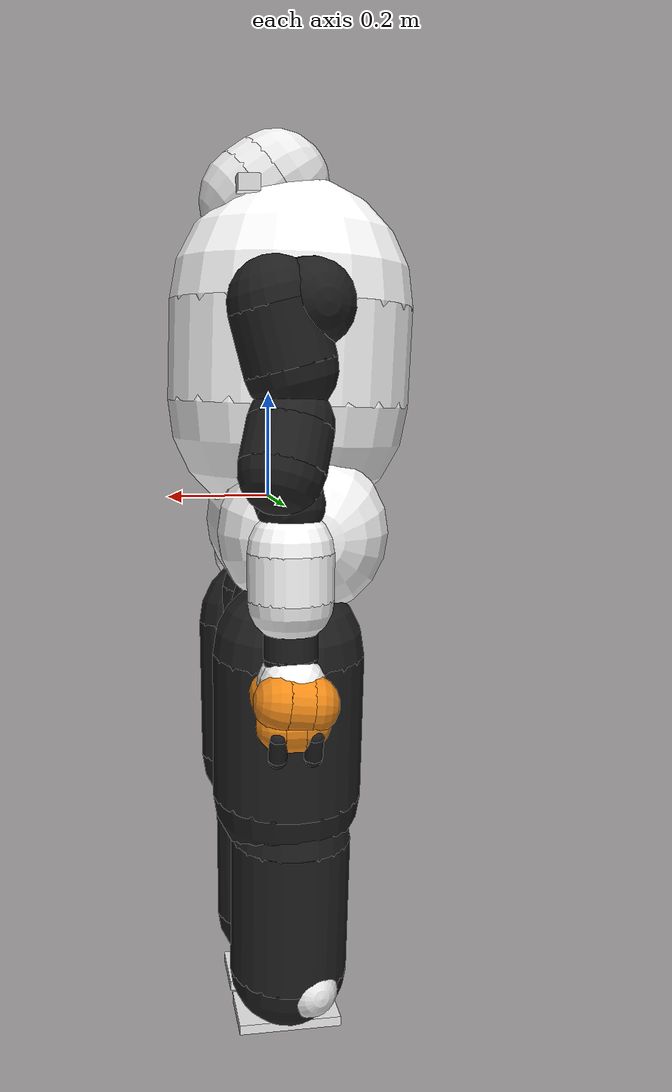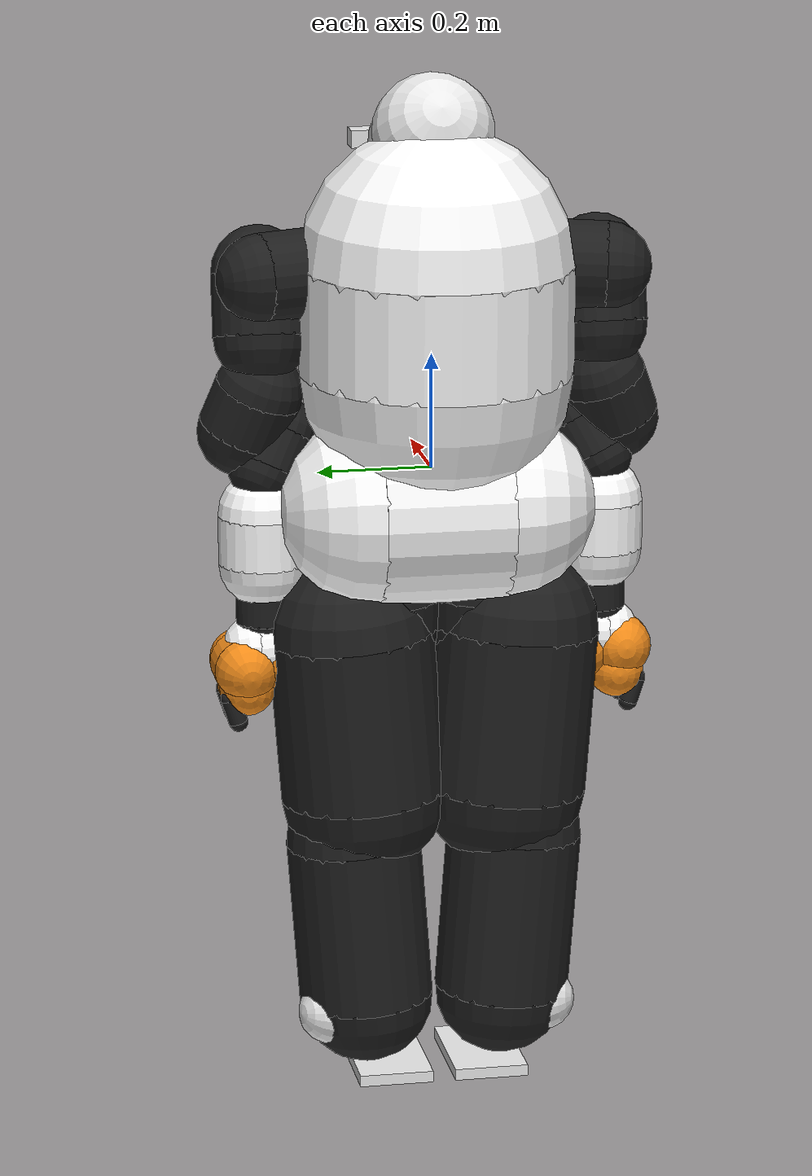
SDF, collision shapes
<sdf version='1.9'>
  <model name='talos'>
    <link name='base_link'>
      <inertial>
        <pose>-0.05709419 0.00153054 -0.0762521 0 0 0</pose>
        <mass>15.36284</mass>
        <inertia>
          <ixx>0.20105075811000001</ixx>
          <ixy>0.00023244733999999999</ixy>
          <ixz>0.0040167728000000003</ixz>
          <iyy>0.084114967289999995</iyy>
          <iyz>-0.00087206649</iyz>
          <izz>0.23189084139999999</izz>
        </inertia>
      </inertial>
      <collision name='base_link_collision'>
        <pose>-0.0485657 0.111601 -0.05811 1.56838 -0.00213179 -0.00212663</pose>
        <geometry>
          <sphere>
            <radius>0.16382936354183919</radius>
          </sphere>
        </geometry>
        <surface>
          <contact>
            <ode/>
          </contact>
          <friction>
            <ode>
              <mu>0.90000000000000002</mu>
              <mu2>0.90000000000000002</mu2>
            </ode>
          </friction>
        </surface>
      </collision>
      <collision name='base_link_collision_1'>
        <pose>-0.0488028 0.000376009 -0.0578407 1.56838 -0.00213179 -0.00212663</pose>
        <geometry>
          <cylinder>
            <length>0.2224509680364736</length>
            <radius>0.16382936354183919</radius>
          </cylinder>
        </geometry>
        <surface>
          <contact>
            <ode/>
          </contact>
          <friction>
            <ode>
              <mu>0.90000000000000002</mu>
              <mu2>0.90000000000000002</mu2>
            </ode>
          </friction>
        </surface>
      </collision>
      <collision name='base_link_collision_2'>
        <pose>-0.0490399 -0.110849 -0.0575714 1.56838 -0.00213179 -0.00212663</pose>
        <geometry>
          <sphere>
            <radius>0.16382936354183919</radius>
          </sphere>
        </geometry>
        <surface>
          <contact>
            <ode/>
          </contact>
          <friction>
            <ode>
              <mu>0.90000000000000002</mu>
              <mu2>0.90000000000000002</mu2>
            </ode>
          </friction>
        </surface>
      </collision>
      <visual name='base_link_visual'>
        <pose>0 0 0 0 0 0</pose>
        <geometry>
          <mesh>
            <scale>1 1 1</scale>
            <uri>meshes/torso/base_link.STL</uri>
          </mesh>
        </geometry>
        <material>
          <diffuse>1 1 1 1</diffuse>
          <ambient>1 1 1 1</ambient>
        </material>
      </visual>
    </link>
    <joint name='leg_left_1_joint' type='revolute'>
      <pose relative_to='base_link'>-0.02 0.08500000000000001 -0.27105 0 0 0</pose>
      <parent>base_link</parent>
      <child>leg_left_1_link</child>
      <axis>
        <xyz>0 0 1</xyz>
        <limit>
          <lower>-0.3490658503988659</lower>
          <upper>1.570796326794897</upper>
          <effort>100</effort>
          <velocity>3.8700000000000001</velocity>
        </limit>
        <dynamics>
          <damping>0</damping>
          <friction>0</friction>
          <spring_reference>0</spring_reference>
          <spring_stiffness>0</spring_stiffness>
        </dynamics>
      </axis>
      <physics>
        <ode>
          <implicit_spring_damper>true</implicit_spring_damper>
          <cfm_damping>true</cfm_damping>
          <limit>
            <cfm>0</cfm>
            <erp>0.20000000000000001</erp>
          </limit>
        </ode>
      </physics>
    </joint>
    <link name='leg_left_1_link'>
      <pose relative_to='leg_left_1_joint'>0 0 0 0 0 0</pose>
      <inertial>
        <pose>0.08472839 0.10997434 0.01705898 0 0 0</pose>
        <mass>2.2350089999999998</mass>
        <inertia>
          <ixx>0.010498489999999999</ixx>
          <ixy>-4.0970000000000002e-05</ixy>
          <ixz>9.7709999999999998e-05</ixz>
          <iyy>0.0053408600000000002</iyy>
          <iyz>0.0011949</iyz>
          <izz>0.0070859499999999997</izz>
        </inertia>
      </inertial>
      <collision name='leg_left_1_link_collision'>
        <pose>0.00653137 -0.00107636 0.0620231 -3.12031 0.1433 -2.84723</pose>
        <geometry>
          <sphere>
            <radius>0.1003888451630799</radius>
          </sphere>
        </geometry>
        <surface>
          <contact>
            <ode/>
          </contact>
          <friction>
            <ode>
              <mu>0.90000000000000002</mu>
              <mu2>0.90000000000000002</mu2>
            </ode>
          </friction>
        </surface>
      </collision>
      <collision name='leg_left_1_link_collision_1'>
        <pose>0.0106955 -0.000462282 0.0331702 -3.12031 0.1433 -2.84723</pose>
        <geometry>
          <cylinder>
            <length>0.058316498699378369</length>
            <radius>0.1003888451630799</radius>
          </cylinder>
        </geometry>
        <surface>
          <contact>
            <ode/>
          </contact>
          <friction>
            <ode>
              <mu>0.90000000000000002</mu>
              <mu2>0.90000000000000002</mu2>
            </ode>
          </friction>
        </surface>
      </collision>
      <collision name='leg_left_1_link_collision_2'>
        <pose>0.0148595 0.000151801 0.00431736 -3.12031 0.1433 -2.84723</pose>
        <geometry>
          <sphere>
            <radius>0.1003888451630799</radius>
          </sphere>
        </geometry>
        <surface>
          <contact>
            <ode/>
          </contact>
          <friction>
            <ode>
              <mu>0.90000000000000002</mu>
              <mu2>0.90000000000000002</mu2>
            </ode>
          </friction>
        </surface>
      </collision>
      <visual name='leg_left_1_link_visual'>
        <pose>0 0 0 0 0 0</pose>
        <geometry>
          <mesh>
            <scale>1 1 1</scale>
            <uri>meshes/v2/hip_z_lo_res.stl</uri>
          </mesh>
        </geometry>
        <material>
          <script>
            <name>Gazebo/FlatBlack</name>
            <uri>file://media/materials/scripts/gazebo.material</uri>
          </script>
          <diffuse>0.25 0.25 0.25 1</diffuse>
          <ambient>0.25 0.25 0.25 1</ambient>
        </material>
      </visual>
    </link>
    <joint name='leg_left_2_joint' type='revolute'>
      <pose relative_to='leg_left_1_link'>0 0 0 0 0 0</pose>
      <parent>leg_left_1_link</parent>
      <child>leg_left_2_link</child>
      <axis>
        <xyz>1 0 0</xyz>
        <limit>
          <lower>-0.52359999999999995</lower>
          <upper>0.52359999999999995</upper>
          <effort>160</effort>
          <velocity>5.7999999999999998</velocity>
        </limit>
        <dynamics>
          <damping>0</damping>
          <friction>0</friction>
          <spring_reference>0</spring_reference>
          <spring_stiffness>0</spring_stiffness>
        </dynamics>
      </axis>
      <physics>
        <ode>
          <implicit_spring_damper>true</implicit_spring_damper>
          <cfm_damping>true</cfm_damping>
          <limit>
            <cfm>0</cfm>
            <erp>0.20000000000000001</erp>
          </limit>
        </ode>
      </physics>
    </joint>
    <link name='leg_left_2_link'>
      <pose relative_to='leg_left_2_joint'>0 0 0 0 0 0</pose>
      <inertial>
        <pose>-0.00704703 0.02592659 0.00273385 0 0 0</pose>
        <mass>1.4909520000000001</mass>
        <inertia>
          <ixx>0.0049715225900000002</ixx>
          <ixy>-0.0001311358</ixy>
          <ixz>-4.8664800000000002e-06</ixz>
          <iyy>0.0019055099300000001</iyy>
          <iyz>4.5853809999999999e-05</iyz>
          <izz>0.0047428975399999998</izz>
        </inertia>
      </inertial>
      <collision name='leg_left_2_link_collision'>
        <pose>-0.0163525 -0.0136729 0.000327785 -1.55227 -0.0161651 0.0158683</pose>
        <geometry>
          <sphere>
            <radius>0.065228014094609946</radius>
          </sphere>
        </geometry>
        <surface>
          <contact>
            <ode/>
          </contact>
          <friction>
            <ode>
              <mu>0.90000000000000002</mu>
              <mu2>0.90000000000000002</mu2>
            </ode>
          </friction>
        </surface>
      </collision>
      <collision name='leg_left_2_link_collision_1'>
        <pose>-0.0170509 0.029524 0.00112826 -1.55227 -0.0161651 0.0158683</pose>
        <geometry>
          <cylinder>
            <length>0.086420044518244921</length>
            <radius>0.065228014094609946</radius>
          </cylinder>
        </geometry>
        <surface>
          <contact>
            <ode/>
          </contact>
          <friction>
            <ode>
              <mu>0.90000000000000002</mu>
              <mu2>0.90000000000000002</mu2>
            </ode>
          </friction>
        </surface>
      </collision>
      <collision name='leg_left_2_link_collision_2'>
        <pose>-0.0177494 0.07272099999999999 0.00192874 -1.55227 -0.0161651 0.0158683</pose>
        <geometry>
          <sphere>
            <radius>0.065228014094609946</radius>
          </sphere>
        </geometry>
        <surface>
          <contact>
            <ode/>
          </contact>
          <friction>
            <ode>
              <mu>0.90000000000000002</mu>
              <mu2>0.90000000000000002</mu2>
            </ode>
          </friction>
        </surface>
      </collision>
      <visual name='leg_left_2_link_visual'>
        <pose>0 0 0 0 0 0</pose>
        <geometry>
          <mesh>
            <scale>1 1 1</scale>
            <uri>meshes/v2/hip_x_lo_res.stl</uri>
          </mesh>
        </geometry>
        <material>
          <script>
            <name>Gazebo/FlatBlack</name>
            <uri>file://media/materials/scripts/gazebo.material</uri>
          </script>
          <diffuse>0.25 0.25 0.25 1</diffuse>
          <ambient>0.25 0.25 0.25 1</ambient>
        </material>
      </visual>
    </link>
    <joint name='leg_left_3_joint' type='revolute'>
      <pose relative_to='leg_left_2_link'>0 0 0 0 0 0</pose>
      <parent>leg_left_2_link</parent>
      <child>leg_left_3_link</child>
      <axis>
        <xyz>0 1 0</xyz>
        <limit>
          <lower>-2.0950000000000002</lower>
          <upper>0.69999999999999996</upper>
          <effort>160</effort>
          <velocity>5.7999999999999998</velocity>
        </limit>
        <dynamics>
          <damping>0</damping>
          <friction>0</friction>
          <spring_reference>0</spring_reference>
          <spring_stiffness>0</spring_stiffness>
        </dynamics>
      </axis>
      <physics>
        <ode>
          <implicit_spring_damper>true</implicit_spring_damper>
          <cfm_damping>true</cfm_damping>
          <limit>
            <cfm>0</cfm>
            <erp>0.20000000000000001</erp>
          </limit>
        </ode>
      </physics>
    </joint>
    <link name='leg_left_3_link'>
      <pose relative_to='leg_left_3_joint'>0 0 0 0 0 0</pose>
      <inertial>
        <pose>0.0058523 0.06369669999999999 -0.18339564 0 0 0</pose>
        <mass>6.2398709999999999</mass>
        <inertia>
          <ixx>0.15337403915</ixx>
          <ixy>0.00068913396000000004</ixy>
          <ixz>0.0016803436599999999</ixz>
          <iyy>0.13648139345999999</iyy>
          <iyz>-0.02187635445</iyz>
          <izz>0.030015948850000002</izz>
        </inertia>
      </inertial>
      <collision name='leg_left_3_link_collision'>
        <pose>0.00475684 0.0387611 -0.305131 -0.07705200000000001 0.00015972 -6.15642e-06</pose>
        <geometry>
          <sphere>
            <radius>0.1455791214721025</radius>
          </sphere>
        </geometry>
        <surface>
          <contact>
            <ode/>
          </contact>
          <friction>
            <ode>
              <mu>0.90000000000000002</mu>
              <mu2>0.90000000000000002</mu2>
            </ode>
          </friction>
        </surface>
      </collision>
      <collision name='leg_left_3_link_collision_1'>
        <pose>0.00478022 0.0500287 -0.159187 -0.07705200000000001 0.00015972 -6.15642e-06</pose>
        <geometry>
          <cylinder>
            <length>0.29275626620252521</length>
            <radius>0.1455791214721025</radius>
          </cylinder>
        </geometry>
        <surface>
          <contact>
            <ode/>
          </contact>
          <friction>
            <ode>
              <mu>0.90000000000000002</mu>
              <mu2>0.90000000000000002</mu2>
            </ode>
          </friction>
        </surface>
      </collision>
      <collision name='leg_left_3_link_collision_2'>
        <pose>0.0048036 0.0612963 -0.0132432 -0.07705200000000001 0.00015972 -6.15642e-06</pose>
        <geometry>
          <sphere>
            <radius>0.1455791214721025</radius>
          </sphere>
        </geometry>
        <surface>
          <contact>
            <ode/>
          </contact>
          <friction>
            <ode>
              <mu>0.90000000000000002</mu>
              <mu2>0.90000000000000002</mu2>
            </ode>
          </friction>
        </surface>
      </collision>
      <visual name='leg_left_3_link_visual'>
        <pose>0 0 0 0 0 0</pose>
        <geometry>
          <mesh>
            <scale>1 1 1</scale>
            <uri>meshes/v2/hip_y_lo_res.stl</uri>
          </mesh>
        </geometry>
        <material>
          <script>
            <name>Gazebo/FlatBlack</name>
            <uri>file://media/materials/scripts/gazebo.material</uri>
          </script>
          <diffuse>0.25 0.25 0.25 1</diffuse>
          <ambient>0.25 0.25 0.25 1</ambient>
        </material>
      </visual>
    </link>
    <joint name='leg_left_4_joint' type='revolute'>
      <pose relative_to='leg_left_3_link'>0 0 -0.38 0 0 0</pose>
      <parent>leg_left_3_link</parent>
      <child>leg_left_4_link</child>
      <axis>
        <xyz>0 1 0</xyz>
        <limit>
          <lower>0</lower>
          <upper>2.6179999999999999</upper>
          <effort>400</effort>
          <velocity>7</velocity>
        </limit>
        <dynamics>
          <damping>0</damping>
          <friction>0</friction>
          <spring_reference>0</spring_reference>
          <spring_stiffness>0</spring_stiffness>
        </dynamics>
      </axis>
      <physics>
        <ode>
          <implicit_spring_damper>true</implicit_spring_damper>
          <cfm_damping>true</cfm_damping>
          <limit>
            <cfm>0</cfm>
            <erp>0.20000000000000001</erp>
          </limit>
        </ode>
      </physics>
    </joint>
    <link name='leg_left_4_link'>
      <pose relative_to='leg_left_4_joint'>0 0 0 0 0 0</pose>
      <inertial>
        <pose>0.01317717 0.02917508 -0.11594602 0 0 0</pose>
        <mass>3.759951</mass>
        <inertia>
          <ixx>0.04287677484</ixx>
          <ixy>0.00043705396999999999</ixy>
          <ixz>0.00078292368000000003</ixz>
          <iyy>0.035989069710000002</iyy>
          <iyz>0.00037717693999999999</iyz>
          <izz>0.013647915639999999</izz>
        </inertia>
      </inertial>
      <collision name='leg_left_4_link_collision'>
        <pose>0.00163993 0.0368989 -0.301909 -0.07472390000000001 -0.005371850000000002 0.0002007970000000001</pose>
        <geometry>
          <sphere>
            <radius>0.1184924950609377</radius>
          </sphere>
        </geometry>
        <surface>
          <contact>
            <ode/>
          </contact>
          <friction>
            <ode>
              <mu>0.90000000000000002</mu>
              <mu2>0.90000000000000002</mu2>
            </ode>
          </friction>
        </surface>
      </collision>
      <collision name='leg_left_4_link_collision_1'>
        <pose>0.000848448 0.0478982 -0.154983 -0.07472390000000001 -0.005371850000000002 0.0002007970000000001</pose>
        <geometry>
          <cylinder>
            <length>0.29467833417874939</length>
            <radius>0.1184924950609377</radius>
          </cylinder>
        </geometry>
        <surface>
          <contact>
            <ode/>
          </contact>
          <friction>
            <ode>
              <mu>0.90000000000000002</mu>
              <mu2>0.90000000000000002</mu2>
            </ode>
          </friction>
        </surface>
      </collision>
      <collision name='leg_left_4_link_collision_2'>
        <pose>5.69681e-05 0.0588976 -0.008056779999999999 -0.07472390000000001 -0.005371850000000002 0.0002007970000000001</pose>
        <geometry>
          <sphere>
            <radius>0.1184924950609377</radius>
          </sphere>
        </geometry>
        <surface>
          <contact>
            <ode/>
          </contact>
          <friction>
            <ode>
              <mu>0.90000000000000002</mu>
              <mu2>0.90000000000000002</mu2>
            </ode>
          </friction>
        </surface>
      </collision>
      <visual name='leg_left_4_link_visual'>
        <pose>0 0 0 0 0 0</pose>
        <geometry>
          <mesh>
            <scale>1 1 1</scale>
            <uri>meshes/v2/knee_lo_res.stl</uri>
          </mesh>
        </geometry>
        <material>
          <script>
            <name>Gazebo/FlatBlack</name>
            <uri>file://media/materials/scripts/gazebo.material</uri>
          </script>
          <diffuse>0.25 0.25 0.25 1</diffuse>
          <ambient>0.25 0.25 0.25 1</ambient>
        </material>
      </visual>
    </link>
    <joint name='leg_left_5_joint' type='revolute'>
      <pose relative_to='leg_left_4_link'>0 0 -0.325 0 0 0</pose>
      <parent>leg_left_4_link</parent>
      <child>leg_left_5_link</child>
      <axis>
        <xyz>0 1 0</xyz>
        <limit>
          <lower>-1.27</lower>
          <upper>0.68000000000000005</upper>
          <effort>160</effort>
          <velocity>5.7999999999999998</velocity>
        </limit>
        <dynamics>
          <damping>0</damping>
          <friction>0</friction>
          <spring_reference>0</spring_reference>
          <spring_stiffness>0</spring_stiffness>
        </dynamics>
      </axis>
      <physics>
        <ode>
          <implicit_spring_damper>true</implicit_spring_damper>
          <cfm_damping>true</cfm_damping>
          <limit>
            <cfm>0</cfm>
            <erp>0.20000000000000001</erp>
          </limit>
        </ode>
      </physics>
    </joint>
    <link name='leg_left_5_link'>
      <pose relative_to='leg_left_5_joint'>0 0 0 0 0 0</pose>
      <inertial>
        <pose>-0.01400838 0.04180064 0.03820186 0 0 0</pose>
        <mass>1.2909600000000001</mass>
        <inertia>
          <ixx>0.011434308190000001</ixx>
          <ixy>0.00096978272999999999</ixy>
          <ixz>0.00039976581000000002</ixz>
          <iyy>0.0088897431199999998</iyy>
          <iyz>-0.0027780866699999998</iyz>
          <izz>0.0050637387500000004</izz>
        </inertia>
      </inertial>
      <collision name='leg_left_5_link_collision'>
        <pose>-0.0304137 0.105995 0.00632637 1.64994 0.303997 0.3286299999999999</pose>
        <geometry>
          <sphere>
            <radius>0.056285651716761462</radius>
          </sphere>
        </geometry>
        <surface>
          <contact>
            <ode/>
          </contact>
          <friction>
            <ode>
              <mu>0.90000000000000002</mu>
              <mu2>0.90000000000000002</mu2>
            </ode>
          </friction>
        </surface>
      </collision>
      <collision name='leg_left_5_link_collision_1'>
        <pose>-0.0118876 0.0471272 0.00165754 1.64994 0.303997 0.3286299999999999</pose>
        <geometry>
          <cylinder>
            <length>0.12378102303209609</length>
            <radius>0.056285651716761462</radius>
          </cylinder>
        </geometry>
        <surface>
          <contact>
            <ode/>
          </contact>
          <friction>
            <ode>
              <mu>0.90000000000000002</mu>
              <mu2>0.90000000000000002</mu2>
            </ode>
          </friction>
        </surface>
      </collision>
      <collision name='leg_left_5_link_collision_2'>
        <pose>0.00663845 -0.0117406 -0.00301129 1.64994 0.303997 0.3286299999999999</pose>
        <geometry>
          <sphere>
            <radius>0.056285651716761462</radius>
          </sphere>
        </geometry>
        <surface>
          <contact>
            <ode/>
          </contact>
          <friction>
            <ode>
              <mu>0.90000000000000002</mu>
              <mu2>0.90000000000000002</mu2>
            </ode>
          </friction>
        </surface>
      </collision>
      <visual name='leg_left_5_link_visual'>
        <pose>0 0 0 0 0 0</pose>
        <geometry>
          <mesh>
            <scale>1 1 1</scale>
            <uri>meshes/v2/ankle_Y_lo_res.stl</uri>
          </mesh>
        </geometry>
        <material>
          <script>
            <name>Gazebo/White</name>
            <uri>file://media/materials/scripts/gazebo.material</uri>
          </script>
          <diffuse>0.875 0.875 0.875 1</diffuse>
          <ambient>0.875 0.875 0.875 1</ambient>
        </material>
      </visual>
    </link>
    <joint name='leg_left_6_joint' type='revolute'>
      <pose relative_to='leg_left_5_link'>0 0 0 0 0 0</pose>
      <parent>leg_left_5_link</parent>
      <child>leg_left_6_link</child>
      <axis>
        <xyz>1 0 0</xyz>
        <limit>
          <lower>-0.52359999999999995</lower>
          <upper>0.52359999999999995</upper>
          <effort>100</effort>
          <velocity>4.7999999999999998</velocity>
        </limit>
        <dynamics>
          <damping>0</damping>
          <friction>0</friction>
          <spring_reference>0</spring_reference>
          <spring_stiffness>0</spring_stiffness>
        </dynamics>
      </axis>
      <physics>
        <ode>
          <implicit_spring_damper>true</implicit_spring_damper>
          <cfm_damping>true</cfm_damping>
          <limit>
            <cfm>0</cfm>
            <erp>0.20000000000000001</erp>
          </limit>
          <provide_feedback>true</provide_feedback>
        </ode>
        <provide_feedback>true</provide_feedback>
      </physics>
      <sensor name='ankle_left_ft_sensor' type='force_torque'>
        <always_on>true</always_on>
        <update_rate>1000</update_rate>
        <visualize>true</visualize>
        <force_torque>
          <frame>child</frame>
          <measure_direction>child_to_parent</measure_direction>
        </force_torque>
      </sensor>
    </joint>
    <link name='leg_left_6_link'>
      <pose relative_to='leg_left_6_joint'>0 0 0 0 0 0</pose>
      <inertial>
        <pose>-0.02022012805516699 -0.0005119359407204872 -0.06016739177635151 0 0 0</pose>
        <mass>1.6077729999999999</mass>
        <inertia>
          <ixx>0.0045123455110069781</ixx>
          <ixy>-6.754090196766338e-05</ixy>
          <ixz>0.001147692510930919</ixz>
          <iyy>0.0075568146185711494</iyy>
          <iyz>3.9672683498003288e-05</iyz>
          <izz>0.005613183751937781</izz>
        </inertia>
      </inertial>
      <collision name='leg_left_6_link_collision'>
        <pose>0 0 -0.1 0 0 0</pose>
        <geometry>
          <box>
            <size>0.21 0.13 0.02</size>
          </box>
        </geometry>
        <surface>
          <contact>
            <ode>
              <kp>1000000</kp>
              <kd>100</kd>
              <max_vel>1</max_vel>
              <min_depth>0</min_depth>
            </ode>
          </contact>
          <friction>
            <ode>
              <mu>1</mu>
              <mu2>1</mu2>
              <fdir1>1 0 0</fdir1>
            </ode>
          </friction>
        </surface>
      </collision>
      <visual name='leg_left_6_link_visual'>
        <pose>0 0 0 0 0 0</pose>
        <geometry>
          <mesh>
            <scale>1 1 1</scale>
            <uri>meshes/v2/ankle_X_lo_res.stl</uri>
          </mesh>
        </geometry>
        <material>
          <script>
            <name>Gazebo/White</name>
            <uri>file://media/materials/scripts/gazebo.material</uri>
          </script>
          <diffuse>0.875 0.875 0.875 1</diffuse>
          <ambient>0.875 0.875 0.875 1</ambient>
        </material>
      </visual>
    </link>
    <joint name='leg_right_1_joint' type='revolute'>
      <pose relative_to='base_link'>-0.02 -0.08500000000000001 -0.27105 0 0 0</pose>
      <parent>base_link</parent>
      <child>leg_right_1_link</child>
      <axis>
        <xyz>0 0 1</xyz>
        <limit>
          <lower>-1.570796326794897</lower>
          <upper>0.3490658503988659</upper>
          <effort>100</effort>
          <velocity>3.8700000000000001</velocity>
        </limit>
        <dynamics>
          <damping>0</damping>
          <friction>0</friction>
          <spring_reference>0</spring_reference>
          <spring_stiffness>0</spring_stiffness>
        </dynamics>
      </axis>
      <physics>
        <ode>
          <implicit_spring_damper>true</implicit_spring_damper>
          <cfm_damping>true</cfm_damping>
          <limit>
            <cfm>0</cfm>
            <erp>0.20000000000000001</erp>
          </limit>
        </ode>
      </physics>
    </joint>
    <link name='leg_right_1_link'>
      <pose relative_to='leg_right_1_joint'>0 0 0 0 0 0</pose>
      <inertial>
        <pose>0.08472839 -0.10997434 0.01705898 0 0 0</pose>
        <mass>2.2350089999999998</mass>
        <inertia>
          <ixx>0.010498489999999999</ixx>
          <ixy>4.0970000000000002e-05</ixy>
          <ixz>9.7709999999999998e-05</ixz>
          <iyy>0.0053408600000000002</iyy>
          <iyz>-0.0011949</iyz>
          <izz>0.0070859499999999997</izz>
        </inertia>
      </inertial>
      <collision name='leg_right_1_link_collision'>
        <pose>0.00653137 0.00107636 0.0620231 3.12031 0.1433 2.84723</pose>
        <geometry>
          <sphere>
            <radius>0.1003888451630799</radius>
          </sphere>
        </geometry>
        <surface>
          <contact>
            <ode/>
          </contact>
          <friction>
            <ode>
              <mu>0.90000000000000002</mu>
              <mu2>0.90000000000000002</mu2>
            </ode>
          </friction>
        </surface>
      </collision>
      <collision name='leg_right_1_link_collision_1'>
        <pose>0.0106955 0.000462282 0.0331702 3.12031 0.1433 2.84723</pose>
        <geometry>
          <cylinder>
            <length>0.058316498699378369</length>
            <radius>0.1003888451630799</radius>
          </cylinder>
        </geometry>
        <surface>
          <contact>
            <ode/>
          </contact>
          <friction>
            <ode>
              <mu>0.90000000000000002</mu>
              <mu2>0.90000000000000002</mu2>
            </ode>
          </friction>
        </surface>
      </collision>
      <collision name='leg_right_1_link_collision_2'>
        <pose>0.0148595 -0.000151801 0.00431736 3.12031 0.1433 2.84723</pose>
        <geometry>
          <sphere>
            <radius>0.1003888451630799</radius>
          </sphere>
        </geometry>
        <surface>
          <contact>
            <ode/>
          </contact>
          <friction>
            <ode>
              <mu>0.90000000000000002</mu>
              <mu2>0.90000000000000002</mu2>
            </ode>
          </friction>
        </surface>
      </collision>
      <visual name='leg_right_1_link_visual'>
        <pose>0 0 0 0 0 0</pose>
        <geometry>
          <mesh>
            <scale>1 -1 1</scale>
            <uri>meshes/v2/hip_z_lo_res.stl</uri>
          </mesh>
        </geometry>
        <material>
          <script>
            <name>Gazebo/FlatBlack</name>
            <uri>file://media/materials/scripts/gazebo.material</uri>
          </script>
          <diffuse>0.25 0.25 0.25 1</diffuse>
          <ambient>0.25 0.25 0.25 1</ambient>
        </material>
      </visual>
    </link>
    <joint name='leg_right_2_joint' type='revolute'>
      <pose relative_to='leg_right_1_link'>0 0 0 0 0 0</pose>
      <parent>leg_right_1_link</parent>
      <child>leg_right_2_link</child>
      <axis>
        <xyz>1 0 0</xyz>
        <limit>
          <lower>-0.52359999999999995</lower>
          <upper>0.52359999999999995</upper>
          <effort>160</effort>
          <velocity>5.7999999999999998</velocity>
        </limit>
        <dynamics>
          <damping>0</damping>
          <friction>0</friction>
          <spring_reference>0</spring_reference>
          <spring_stiffness>0</spring_stiffness>
        </dynamics>
      </axis>
      <physics>
        <ode>
          <implicit_spring_damper>true</implicit_spring_damper>
          <cfm_damping>true</cfm_damping>
          <limit>
            <cfm>0</cfm>
            <erp>0.20000000000000001</erp>
          </limit>
        </ode>
      </physics>
    </joint>
    <link name='leg_right_2_link'>
      <pose relative_to='leg_right_2_joint'>0 0 0 0 0 0</pose>
      <inertial>
        <pose>-0.00704703 -0.02592659 0.00273385 0 0 0</pose>
        <mass>1.4909520000000001</mass>
        <inertia>
          <ixx>0.0049715225900000002</ixx>
          <ixy>0.0001311358</ixy>
          <ixz>-4.8664800000000002e-06</ixz>
          <iyy>0.0019055099300000001</iyy>
          <iyz>-4.5853809999999999e-05</iyz>
          <izz>0.0047428975399999998</izz>
        </inertia>
      </inertial>
      <collision name='leg_right_2_link_collision'>
        <pose>-0.0163525 0.0136729 0.000327785 1.55227 -0.0161651 -0.0158683</pose>
        <geometry>
          <sphere>
            <radius>0.065228014094609946</radius>
          </sphere>
        </geometry>
        <surface>
          <contact>
            <ode/>
          </contact>
          <friction>
            <ode>
              <mu>0.90000000000000002</mu>
              <mu2>0.90000000000000002</mu2>
            </ode>
          </friction>
        </surface>
      </collision>
      <collision name='leg_right_2_link_collision_1'>
        <pose>-0.0170509 -0.029524 0.00112826 1.55227 -0.0161651 -0.0158683</pose>
        <geometry>
          <cylinder>
            <length>0.086420044518244921</length>
            <radius>0.065228014094609946</radius>
          </cylinder>
        </geometry>
        <surface>
          <contact>
            <ode/>
          </contact>
          <friction>
            <ode>
              <mu>0.90000000000000002</mu>
              <mu2>0.90000000000000002</mu2>
            </ode>
          </friction>
        </surface>
      </collision>
      <collision name='leg_right_2_link_collision_2'>
        <pose>-0.0177494 -0.07272099999999999 0.00192874 1.55227 -0.0161651 -0.0158683</pose>
        <geometry>
          <sphere>
            <radius>0.065228014094609946</radius>
          </sphere>
        </geometry>
        <surface>
          <contact>
            <ode/>
          </contact>
          <friction>
            <ode>
              <mu>0.90000000000000002</mu>
              <mu2>0.90000000000000002</mu2>
            </ode>
          </friction>
        </surface>
      </collision>
      <visual name='leg_right_2_link_visual'>
        <pose>0 0 0 0 0 0</pose>
        <geometry>
          <mesh>
            <scale>1 -1 1</scale>
            <uri>meshes/v2/hip_x_lo_res.stl</uri>
          </mesh>
        </geometry>
        <material>
          <script>
            <name>Gazebo/FlatBlack</name>
            <uri>file://media/materials/scripts/gazebo.material</uri>
          </script>
          <diffuse>0.25 0.25 0.25 1</diffuse>
          <ambient>0.25 0.25 0.25 1</ambient>
        </material>
      </visual>
    </link>
    <joint name='leg_right_3_joint' type='revolute'>
      <pose relative_to='leg_right_2_link'>0 0 0 0 0 0</pose>
      <parent>leg_right_2_link</parent>
      <child>leg_right_3_link</child>
      <axis>
        <xyz>0 1 0</xyz>
        <limit>
          <lower>-2.0950000000000002</lower>
          <upper>0.69999999999999996</upper>
          <effort>160</effort>
          <velocity>5.7999999999999998</velocity>
        </limit>
        <dynamics>
          <damping>0</damping>
          <friction>0</friction>
          <spring_reference>0</spring_reference>
          <spring_stiffness>0</spring_stiffness>
        </dynamics>
      </axis>
      <physics>
        <ode>
          <implicit_spring_damper>true</implicit_spring_damper>
          <cfm_damping>true</cfm_damping>
          <limit>
            <cfm>0</cfm>
            <erp>0.20000000000000001</erp>
          </limit>
        </ode>
      </physics>
    </joint>
    <link name='leg_right_3_link'>
      <pose relative_to='leg_right_3_joint'>0 0 0 0 0 0</pose>
      <inertial>
        <pose>0.0058523 -0.06369669999999999 -0.18339564 0 0 0</pose>
        <mass>6.2398709999999999</mass>
        <inertia>
          <ixx>0.15337403915</ixx>
          <ixy>-0.00068913396000000004</ixy>
          <ixz>0.0016803436599999999</ixz>
          <iyy>0.13648139345999999</iyy>
          <iyz>0.02187635445</iyz>
          <izz>0.030015948850000002</izz>
        </inertia>
      </inertial>
      <collision name='leg_right_3_link_collision'>
        <pose>0.00475684 -0.0387611 -0.305131 0.07705200000000001 0.00015972 6.15642e-06</pose>
        <geometry>
          <sphere>
            <radius>0.1455791214721025</radius>
          </sphere>
        </geometry>
        <surface>
          <contact>
            <ode/>
          </contact>
          <friction>
            <ode>
              <mu>0.90000000000000002</mu>
              <mu2>0.90000000000000002</mu2>
            </ode>
          </friction>
        </surface>
      </collision>
      <collision name='leg_right_3_link_collision_1'>
        <pose>0.00478022 -0.0500287 -0.159187 0.07705200000000001 0.00015972 6.15642e-06</pose>
        <geometry>
          <cylinder>
            <length>0.29275626620252521</length>
            <radius>0.1455791214721025</radius>
          </cylinder>
        </geometry>
        <surface>
          <contact>
            <ode/>
          </contact>
          <friction>
            <ode>
              <mu>0.90000000000000002</mu>
              <mu2>0.90000000000000002</mu2>
            </ode>
          </friction>
        </surface>
      </collision>
      <collision name='leg_right_3_link_collision_2'>
        <pose>0.0048036 -0.0612963 -0.0132432 0.07705200000000001 0.00015972 6.15642e-06</pose>
        <geometry>
          <sphere>
            <radius>0.1455791214721025</radius>
          </sphere>
        </geometry>
        <surface>
          <contact>
            <ode/>
          </contact>
          <friction>
            <ode>
              <mu>0.90000000000000002</mu>
              <mu2>0.90000000000000002</mu2>
            </ode>
          </friction>
        </surface>
      </collision>
      <visual name='leg_right_3_link_visual'>
        <pose>0 0 0 0 0 0</pose>
        <geometry>
          <mesh>
            <scale>1 -1 1</scale>
            <uri>meshes/v2/hip_y_lo_res.stl</uri>
          </mesh>
        </geometry>
        <material>
          <script>
            <name>Gazebo/FlatBlack</name>
            <uri>file://media/materials/scripts/gazebo.material</uri>
          </script>
          <diffuse>0.25 0.25 0.25 1</diffuse>
          <ambient>0.25 0.25 0.25 1</ambient>
        </material>
      </visual>
    </link>
    <joint name='leg_right_4_joint' type='revolute'>
      <pose relative_to='leg_right_3_link'>0 0 -0.38 0 0 0</pose>
      <parent>leg_right_3_link</parent>
      <child>leg_right_4_link</child>
      <axis>
        <xyz>0 1 0</xyz>
        <limit>
          <lower>0</lower>
          <upper>2.6179999999999999</upper>
          <effort>400</effort>
          <velocity>7</velocity>
        </limit>
        <dynamics>
          <damping>0</damping>
          <friction>0</friction>
          <spring_reference>0</spring_reference>
          <spring_stiffness>0</spring_stiffness>
        </dynamics>
      </axis>
      <physics>
        <ode>
          <implicit_spring_damper>true</implicit_spring_damper>
          <cfm_damping>true</cfm_damping>
          <limit>
            <cfm>0</cfm>
            <erp>0.20000000000000001</erp>
          </limit>
        </ode>
      </physics>
    </joint>
    <link name='leg_right_4_link'>
      <pose relative_to='leg_right_4_joint'>0 0 0 0 0 0</pose>
      <inertial>
        <pose>0.01317717 -0.02917508 -0.11594602 0 0 0</pose>
        <mass>3.759951</mass>
        <inertia>
          <ixx>0.04287677484</ixx>
          <ixy>-0.00043705396999999999</ixy>
          <ixz>0.00078292368000000003</ixz>
          <iyy>0.035989069710000002</iyy>
          <iyz>-0.00037717693999999999</iyz>
          <izz>0.013647915639999999</izz>
        </inertia>
      </inertial>
      <collision name='leg_right_4_link_collision'>
        <pose>0.00163993 -0.0368989 -0.301909 0.07472390000000001 -0.005371850000000002 -0.0002007970000000001</pose>
        <geometry>
          <sphere>
            <radius>0.1184924950609377</radius>
          </sphere>
        </geometry>
        <surface>
          <contact>
            <ode/>
          </contact>
          <friction>
            <ode>
              <mu>0.90000000000000002</mu>
              <mu2>0.90000000000000002</mu2>
            </ode>
          </friction>
        </surface>
      </collision>
      <collision name='leg_right_4_link_collision_1'>
        <pose>0.000848448 -0.0478982 -0.154983 0.07472390000000001 -0.005371850000000002 -0.0002007970000000001</pose>
        <geometry>
          <cylinder>
            <length>0.29467833417874939</length>
            <radius>0.1184924950609377</radius>
          </cylinder>
        </geometry>
        <surface>
          <contact>
            <ode/>
          </contact>
          <friction>
            <ode>
              <mu>0.90000000000000002</mu>
              <mu2>0.90000000000000002</mu2>
            </ode>
          </friction>
        </surface>
      </collision>
      <collision name='leg_right_4_link_collision_2'>
        <pose>5.69681e-05 -0.0588976 -0.008056779999999999 0.07472390000000001 -0.005371850000000002 -0.0002007970000000001</pose>
        <geometry>
          <sphere>
            <radius>0.1184924950609377</radius>
          </sphere>
        </geometry>
        <surface>
          <contact>
            <ode/>
          </contact>
          <friction>
            <ode>
              <mu>0.90000000000000002</mu>
              <mu2>0.90000000000000002</mu2>
            </ode>
          </friction>
        </surface>
      </collision>
      <visual name='leg_right_4_link_visual'>
        <pose>0 0 0 0 0 0</pose>
        <geometry>
          <mesh>
            <scale>1 -1 1</scale>
            <uri>meshes/v2/knee_lo_res.stl</uri>
          </mesh>
        </geometry>
        <material>
          <script>
            <name>Gazebo/FlatBlack</name>
            <uri>file://media/materials/scripts/gazebo.material</uri>
          </script>
          <diffuse>0.25 0.25 0.25 1</diffuse>
          <ambient>0.25 0.25 0.25 1</ambient>
        </material>
      </visual>
    </link>
    <joint name='leg_right_5_joint' type='revolute'>
      <pose relative_to='leg_right_4_link'>0 0 -0.325 0 0 0</pose>
      <parent>leg_right_4_link</parent>
      <child>leg_right_5_link</child>
      <axis>
        <xyz>0 1 0</xyz>
        <limit>
          <lower>-1.27</lower>
          <upper>0.68000000000000005</upper>
          <effort>160</effort>
          <velocity>5.7999999999999998</velocity>
        </limit>
        <dynamics>
          <damping>0</damping>
          <friction>0</friction>
          <spring_reference>0</spring_reference>
          <spring_stiffness>0</spring_stiffness>
        </dynamics>
      </axis>
      <physics>
        <ode>
          <implicit_spring_damper>true</implicit_spring_damper>
          <cfm_damping>true</cfm_damping>
          <limit>
            <cfm>0</cfm>
            <erp>0.20000000000000001</erp>
          </limit>
        </ode>
      </physics>
    </joint>
    <link name='leg_right_5_link'>
      <pose relative_to='leg_right_5_joint'>0 0 0 0 0 0</pose>
      <inertial>
        <pose>-0.01400838 -0.04180064 0.03820186 0 0 0</pose>
        <mass>1.2909600000000001</mass>
        <inertia>
          <ixx>0.011434308190000001</ixx>
          <ixy>-0.00096978272999999999</ixy>
          <ixz>0.00039976581000000002</ixz>
          <iyy>0.0088897431199999998</iyy>
          <iyz>0.0027780866699999998</iyz>
          <izz>0.0050637387500000004</izz>
        </inertia>
      </inertial>
      <collision name='leg_right_5_link_collision'>
        <pose>-0.0304137 -0.105995 0.00632637 -1.64994 0.303997 -0.3286299999999999</pose>
        <geometry>
          <sphere>
            <radius>0.056285651716761462</radius>
          </sphere>
        </geometry>
        <surface>
          <contact>
            <ode/>
          </contact>
          <friction>
            <ode>
              <mu>0.90000000000000002</mu>
              <mu2>0.90000000000000002</mu2>
            </ode>
          </friction>
        </surface>
      </collision>
      <collision name='leg_right_5_link_collision_1'>
        <pose>-0.0118876 -0.0471272 0.00165754 -1.64994 0.303997 -0.3286299999999999</pose>
        <geometry>
          <cylinder>
            <length>0.12378102303209609</length>
            <radius>0.056285651716761462</radius>
          </cylinder>
        </geometry>
        <surface>
          <contact>
            <ode/>
          </contact>
          <friction>
            <ode>
              <mu>0.90000000000000002</mu>
              <mu2>0.90000000000000002</mu2>
            </ode>
          </friction>
        </surface>
      </collision>
      <collision name='leg_right_5_link_collision_2'>
        <pose>0.00663845 0.0117406 -0.00301129 -1.64994 0.303997 -0.3286299999999999</pose>
        <geometry>
          <sphere>
            <radius>0.056285651716761462</radius>
          </sphere>
        </geometry>
        <surface>
          <contact>
            <ode/>
          </contact>
          <friction>
            <ode>
              <mu>0.90000000000000002</mu>
              <mu2>0.90000000000000002</mu2>
            </ode>
          </friction>
        </surface>
      </collision>
      <visual name='leg_right_5_link_visual'>
        <pose>0 0 0 0 0 0</pose>
        <geometry>
          <mesh>
            <scale>1 -1 1</scale>
            <uri>meshes/v2/ankle_Y_lo_res.stl</uri>
          </mesh>
        </geometry>
        <material>
          <script>
            <name>Gazebo/White</name>
            <uri>file://media/materials/scripts/gazebo.material</uri>
          </script>
          <diffuse>0.875 0.875 0.875 1</diffuse>
          <ambient>0.875 0.875 0.875 1</ambient>
        </material>
      </visual>
    </link>
    <joint name='leg_right_6_joint' type='revolute'>
      <pose relative_to='leg_right_5_link'>0 0 0 0 0 0</pose>
      <parent>leg_right_5_link</parent>
      <child>leg_right_6_link</child>
      <axis>
        <xyz>1 0 0</xyz>
        <limit>
          <lower>-0.52359999999999995</lower>
          <upper>0.52359999999999995</upper>
          <effort>100</effort>
          <velocity>4.7999999999999998</velocity>
        </limit>
        <dynamics>
          <damping>0</damping>
          <friction>0</friction>
          <spring_reference>0</spring_reference>
          <spring_stiffness>0</spring_stiffness>
        </dynamics>
      </axis>
      <physics>
        <ode>
          <implicit_spring_damper>true</implicit_spring_damper>
          <cfm_damping>true</cfm_damping>
          <limit>
            <cfm>0</cfm>
            <erp>0.20000000000000001</erp>
          </limit>
          <provide_feedback>true</provide_feedback>
        </ode>
        <provide_feedback>true</provide_feedback>
      </physics>
      <sensor name='ankle_right_ft_sensor' type='force_torque'>
        <always_on>true</always_on>
        <update_rate>1000</update_rate>
        <visualize>true</visualize>
        <force_torque>
          <frame>child</frame>
          <measure_direction>child_to_parent</measure_direction>
        </force_torque>
      </sensor>
    </joint>
    <link name='leg_right_6_link'>
      <pose relative_to='leg_right_6_joint'>0 0 0 0 0 0</pose>
      <inertial>
        <pose>-0.02022012805516699 0.0005119359407204872 -0.06016739177635151 0 0 0</pose>
        <mass>1.6077729999999999</mass>
        <inertia>
          <ixx>0.0045123455110069781</ixx>
          <ixy>6.754090196766338e-05</ixy>
          <ixz>0.001147692510930919</ixz>
          <iyy>0.0075568146185711494</iyy>
          <iyz>-3.9672683498003288e-05</iyz>
          <izz>0.005613183751937781</izz>
        </inertia>
      </inertial>
      <collision name='leg_right_6_link_collision'>
        <pose>0 0 -0.1 0 0 0</pose>
        <geometry>
          <box>
            <size>0.21 0.13 0.02</size>
          </box>
        </geometry>
        <surface>
          <contact>
            <ode>
              <kp>1000000</kp>
              <kd>100</kd>
              <max_vel>1</max_vel>
              <min_depth>0</min_depth>
            </ode>
          </contact>
          <friction>
            <ode>
              <mu>1</mu>
              <mu2>1</mu2>
              <fdir1>1 0 0</fdir1>
            </ode>
          </friction>
        </surface>
      </collision>
      <visual name='leg_right_6_link_visual'>
        <pose>0 0 0 0 0 0</pose>
        <geometry>
          <mesh>
            <scale>1 -1 1</scale>
            <uri>meshes/v2/ankle_X_lo_res.stl</uri>
          </mesh>
        </geometry>
        <material>
          <script>
            <name>Gazebo/White</name>
            <uri>file://media/materials/scripts/gazebo.material</uri>
          </script>
          <diffuse>0.875 0.875 0.875 1</diffuse>
          <ambient>0.875 0.875 0.875 1</ambient>
        </material>
      </visual>
    </link>
    <joint name='torso_1_joint' type='revolute'>
      <pose relative_to='base_link'>0 0 0.0722 0 0 0</pose>
      <parent>base_link</parent>
      <child>torso_1_link</child>
      <axis>
        <xyz>0 0 1</xyz>
        <limit>
          <lower>-1.256637061435917</lower>
          <upper>1.256637061435917</upper>
          <effort>200</effort>
          <velocity>5.4000000000000004</velocity>
        </limit>
        <dynamics>
          <damping>1</damping>
          <friction>1</friction>
          <spring_reference>0</spring_reference>
          <spring_stiffness>0</spring_stiffness>
        </dynamics>
      </axis>
      <physics>
        <ode>
          <implicit_spring_damper>true</implicit_spring_damper>
          <cfm_damping>true</cfm_damping>
          <limit>
            <cfm>0</cfm>
            <erp>0.20000000000000001</erp>
          </limit>
        </ode>
      </physics>
    </joint>
    <link name='torso_1_link'>
      <pose relative_to='torso_1_joint'>0 0 0 0 0 0</pose>
      <inertial>
        <pose>0.00078223 3.528e-05 -0.01782457 0 0 0</pose>
        <mass>2.2946580000000001</mass>
        <inertia>
          <ixx>0.0063850808699999996</ixx>
          <ixy>-7.107e-08</ixy>
          <ixz>-3.065592e-05</ixz>
          <iyy>0.0041025610200000001</iyy>
          <iyz>-1.46946e-06</iyz>
          <izz>0.00622968815</izz>
        </inertia>
      </inertial>
      <collision name='torso_1_link_collision'>
        <pose>-0.00232934 -0.0104948 -0.01235 -1.54415 0.02206980000000001 -0.0214895</pose>
        <geometry>
          <sphere>
            <radius>0.091952314418329517</radius>
          </sphere>
        </geometry>
        <surface>
          <contact>
            <ode/>
          </contact>
          <friction>
            <ode>
              <mu>0.90000000000000002</mu>
              <mu2>0.90000000000000002</mu2>
            </ode>
          </friction>
        </surface>
      </collision>
      <collision name='torso_1_link_collision_1'>
        <pose>-0.00210229 -0.000212158 -0.0120759 -1.54415 0.02206980000000001 -0.0214895</pose>
        <geometry>
          <cylinder>
            <length>0.020577608942189698</length>
            <radius>0.091952314418329517</radius>
          </cylinder>
        </geometry>
        <surface>
          <contact>
            <ode/>
          </contact>
          <friction>
            <ode>
              <mu>0.90000000000000002</mu>
              <mu2>0.90000000000000002</mu2>
            </ode>
          </friction>
        </surface>
      </collision>
      <collision name='torso_1_link_collision_2'>
        <pose>-0.00187524 0.0100705 -0.0118019 -1.54415 0.02206980000000001 -0.0214895</pose>
        <geometry>
          <sphere>
            <radius>0.091952314418329517</radius>
          </sphere>
        </geometry>
        <surface>
          <contact>
            <ode/>
          </contact>
          <friction>
            <ode>
              <mu>0.90000000000000002</mu>
              <mu2>0.90000000000000002</mu2>
            </ode>
          </friction>
        </surface>
      </collision>
      <visual name='torso_1_link_visual'>
        <pose>0 0 0 0 0 0</pose>
        <geometry>
          <mesh>
            <scale>1 1 1</scale>
            <uri>meshes/torso/torso_1.STL</uri>
          </mesh>
        </geometry>
        <material>
          <diffuse>1 1 1 1</diffuse>
          <ambient>1 1 1 1</ambient>
        </material>
      </visual>
    </link>
    <joint name='torso_2_joint' type='revolute'>
      <pose relative_to='torso_1_link'>0 0 0 0 0 0</pose>
      <parent>torso_1_link</parent>
      <child>torso_2_link</child>
      <axis>
        <xyz>0 1 0</xyz>
        <limit>
          <lower>-0.22689280275926291</lower>
          <upper>0.73303828583761843</upper>
          <effort>200</effort>
          <velocity>5.4000000000000004</velocity>
        </limit>
        <dynamics>
          <damping>1</damping>
          <friction>1</friction>
          <spring_reference>0</spring_reference>
          <spring_stiffness>0</spring_stiffness>
        </dynamics>
      </axis>
      <physics>
        <provide_feedback>true</provide_feedback>
        <ode>
          <implicit_spring_damper>true</implicit_spring_damper>
          <cfm_damping>true</cfm_damping>
          <limit>
            <cfm>0</cfm>
            <erp>0.20000000000000001</erp>
          </limit>
          <provide_feedback>true</provide_feedback>
        </ode>
      </physics>
    </joint>
    <link name='torso_2_link'>
      <pose relative_to='torso_2_joint'>0 0 0 0 0 0</pose>
      <inertial>
        <pose>-0.04630000811874449 -0.0009896469640538787 0.1452408860214566 0 0 0</pose>
        <mass>16.984030000000001</mass>
        <inertia>
          <ixx>0.4437725880641008</ixx>
          <ixy>0.00069037516515460572</ixy>
          <ixz>-0.01211777700678765</ixz>
          <iyy>0.29999519863173169</iyy>
          <iyz>-0.0001955675405743494</iyz>
          <izz>0.32210790904719322</izz>
        </inertia>
      </inertial>
      <collision name='torso_2_link_collision'>
        <pose>-0.0381908 -4.93875e-05 0.108256 9.549470000000001e-05 -0.03648310000000001 -1.74216e-06</pose>
        <geometry>
          <sphere>
            <radius>0.2358408976624019</radius>
          </sphere>
        </geometry>
        <surface>
          <contact>
            <ode/>
          </contact>
          <friction>
            <ode>
              <mu>0.90000000000000002</mu>
              <mu2>0.90000000000000002</mu2>
            </ode>
          </friction>
        </surface>
      </collision>
      <collision name='torso_2_link_collision_1'>
        <pose>-0.0416584 -5.84599e-05 0.20326 9.549470000000001e-05 -0.03648310000000001 -1.74216e-06</pose>
        <geometry>
          <cylinder>
            <length>0.19013465851723291</length>
            <radius>0.2358408976624019</radius>
          </cylinder>
        </geometry>
        <surface>
          <contact>
            <ode/>
          </contact>
          <friction>
            <ode>
              <mu>0.90000000000000002</mu>
              <mu2>0.90000000000000002</mu2>
            </ode>
          </friction>
        </surface>
      </collision>
      <collision name='torso_2_link_collision_2'>
        <pose>-0.045126 -6.75323e-05 0.298264 9.549470000000001e-05 -0.03648310000000001 -1.74216e-06</pose>
        <geometry>
          <sphere>
            <radius>0.2358408976624019</radius>
          </sphere>
        </geometry>
        <surface>
          <contact>
            <ode/>
          </contact>
          <friction>
            <ode>
              <mu>0.90000000000000002</mu>
              <mu2>0.90000000000000002</mu2>
            </ode>
          </friction>
        </surface>
      </collision>
      <visual name='torso_2_link_visual'>
        <pose>0 0 0 0 0 0</pose>
        <geometry>
          <mesh>
            <scale>1 1 1</scale>
            <uri>meshes/torso/torso_2.STL</uri>
          </mesh>
        </geometry>
        <material>
          <diffuse>1 1 1 1</diffuse>
          <ambient>1 1 1 1</ambient>
        </material>
      </visual>
      <visual name='torso_2_link_fixed_joint_lump__imu_link_visual_1'>
        <pose>0.04925 0 0.078 3.141592653589793 0 1.570796326794896</pose>
        <geometry>
          <box>
            <size>0.01 0.01 0.01</size>
          </box>
        </geometry>
      </visual>
      <sensor name='imu_sensor' type='imu'>
        <always_on>true</always_on>
        <update_rate>1000</update_rate>
        <imu>
          <noise>
            <type>gaussian</type>
            <rate>
              <mean>0.0</mean>
              <stddev>0.0</stddev>
              <bias_mean>0.000000</bias_mean>
              <bias_stddev>0.0000008</bias_stddev>
            </rate>
            <accel>
              <mean>0.0</mean>
              <stddev>0.0</stddev>
              <bias_mean>0.0</bias_mean>
              <bias_stddev>0.000</bias_stddev>
            </accel>
          </noise>
        </imu>
        <pose>0.04925 0 0.078 3.14159 -0 1.5708</pose>
      </sensor>
    </link>
    <joint name='arm_left_1_joint' type='revolute'>
      <pose relative_to='torso_2_link'>0 0.1575 0.232 0 0 0</pose>
      <parent>torso_2_link</parent>
      <child>arm_left_1_link</child>
      <axis>
        <xyz>0 0 1</xyz>
        <limit>
          <lower>-1.570796326794897</lower>
          <upper>0.78539816339744828</upper>
          <effort>100</effort>
          <velocity>2.7000000000000002</velocity>
        </limit>
        <dynamics>
          <damping>1</damping>
          <friction>1</friction>
          <spring_reference>0</spring_reference>
          <spring_stiffness>0</spring_stiffness>
        </dynamics>
      </axis>
      <physics>
        <ode>
          <implicit_spring_damper>true</implicit_spring_damper>
          <cfm_damping>true</cfm_damping>
          <limit>
            <cfm>0</cfm>
            <erp>0.20000000000000001</erp>
          </limit>
        </ode>
      </physics>
    </joint>
    <link name='arm_left_1_link'>
      <pose relative_to='arm_left_1_joint'>0 0 0 0 0 0</pose>
      <inertial>
        <pose>-0.0002762 0.10060223 0.04437419 0 0 0</pose>
        <mass>2.7145670000000002</mass>
        <inertia>
          <ixx>0.01237818683</ixx>
          <ixy>-3.625571e-05</ixy>
          <ixz>7.1447199999999996e-05</ixz>
          <iyy>0.0041913719999999996</iyy>
          <iyz>-0.00023639064</iyz>
          <izz>0.013581611089999999</izz>
        </inertia>
      </inertial>
      <collision name='arm_left_1_link_collision'>
        <pose>-0.030119 0.141768 0.0465263 1.53256 0.201924 0.194397</pose>
        <geometry>
          <sphere>
            <radius>0.076661652397679497</radius>
          </sphere>
        </geometry>
        <surface>
          <contact>
            <ode/>
          </contact>
          <friction>
            <ode>
              <mu>0.90000000000000002</mu>
              <mu2>0.90000000000000002</mu2>
            </ode>
          </friction>
        </surface>
      </collision>
      <collision name='arm_left_1_link_collision_1'>
        <pose>-0.0172077 0.0787443 0.048937 1.53256 0.201924 0.194397</pose>
        <geometry>
          <cylinder>
            <length>0.12875612953621871</length>
            <radius>0.076661652397679497</radius>
          </cylinder>
        </geometry>
        <surface>
          <contact>
            <ode/>
          </contact>
          <friction>
            <ode>
              <mu>0.90000000000000002</mu>
              <mu2>0.90000000000000002</mu2>
            </ode>
          </friction>
        </surface>
      </collision>
      <collision name='arm_left_1_link_collision_2'>
        <pose>-0.00429634 0.0157203 0.0513477 1.53256 0.201924 0.194397</pose>
        <geometry>
          <sphere>
            <radius>0.076661652397679497</radius>
          </sphere>
        </geometry>
        <surface>
          <contact>
            <ode/>
          </contact>
          <friction>
            <ode>
              <mu>0.90000000000000002</mu>
              <mu2>0.90000000000000002</mu2>
            </ode>
          </friction>
        </surface>
      </collision>
      <visual name='arm_left_1_link_visual'>
        <pose>0 0 0 0 0 0</pose>
        <geometry>
          <mesh>
            <scale>1 1 1</scale>
            <uri>meshes/arm/arm_1.STL</uri>
          </mesh>
        </geometry>
        <material>
          <script>
            <name>Gazebo/FlatBlack</name>
            <uri>file://media/materials/scripts/gazebo.material</uri>
          </script>
          <diffuse>0.25 0.25 0.25 1</diffuse>
          <ambient>0.25 0.25 0.25 1</ambient>
        </material>
      </visual>
    </link>
    <joint name='arm_left_2_joint' type='revolute'>
      <pose relative_to='arm_left_1_link'>0.00493 0.1365 0.04673 0 0 0</pose>
      <parent>arm_left_1_link</parent>
      <child>arm_left_2_link</child>
      <axis>
        <xyz>1 0 0</xyz>
        <limit>
          <lower>0.0087266462599716477</lower>
          <upper>2.871066619530672</upper>
          <effort>100</effort>
          <velocity>3.6600000000000001</velocity>
        </limit>
        <dynamics>
          <damping>1</damping>
          <friction>1</friction>
          <spring_reference>0</spring_reference>
          <spring_stiffness>0</spring_stiffness>
        </dynamics>
      </axis>
      <physics>
        <ode>
          <implicit_spring_damper>true</implicit_spring_damper>
          <cfm_damping>true</cfm_damping>
          <limit>
            <cfm>0</cfm>
            <erp>0.20000000000000001</erp>
          </limit>
        </ode>
      </physics>
    </joint>
    <link name='arm_left_2_link'>
      <pose relative_to='arm_left_2_joint'>0 0 0 0 0 0</pose>
      <inertial>
        <pose>0.01438831 0.00092938 -0.08684268000000001 0 0 0</pose>
        <mass>2.4250859999999999</mass>
        <inertia>
          <ixx>0.012978221010000001</ixx>
          <ixy>1.2087910000000001e-05</ixy>
          <ixz>-0.0032037043299999999</ixz>
          <iyy>0.013808702779999999</iyy>
          <iyz>-0.00012770058999999999</iyz>
          <izz>0.0047885662100000002</izz>
        </inertia>
      </inertial>
      <collision name='arm_left_2_link_collision'>
        <pose>-8.22104e-05 0.00124357 -0.107621 0.009435340000000002 0.2519770000000001 0.00119509</pose>
        <geometry>
          <sphere>
            <radius>0.082464320229024751</radius>
          </sphere>
        </geometry>
        <surface>
          <contact>
            <ode/>
          </contact>
          <friction>
            <ode>
              <mu>0.90000000000000002</mu>
              <mu2>0.90000000000000002</mu2>
            </ode>
          </friction>
        </surface>
      </collision>
      <collision name='arm_left_2_link_collision_1'>
        <pose>0.0133935 0.000749701 -0.0552803 0.009435340000000002 0.2519770000000001 0.00119509</pose>
        <geometry>
          <cylinder>
            <length>0.1080996550780578</length>
            <radius>0.082464320229024751</radius>
          </cylinder>
        </geometry>
        <surface>
          <contact>
            <ode/>
          </contact>
          <friction>
            <ode>
              <mu>0.90000000000000002</mu>
              <mu2>0.90000000000000002</mu2>
            </ode>
          </friction>
        </surface>
      </collision>
      <collision name='arm_left_2_link_collision_2'>
        <pose>0.0268691 0.000255834 -0.00293965 0.009435340000000002 0.2519770000000001 0.00119509</pose>
        <geometry>
          <sphere>
            <radius>0.082464320229024751</radius>
          </sphere>
        </geometry>
        <surface>
          <contact>
            <ode/>
          </contact>
          <friction>
            <ode>
              <mu>0.90000000000000002</mu>
              <mu2>0.90000000000000002</mu2>
            </ode>
          </friction>
        </surface>
      </collision>
      <visual name='arm_left_2_link_visual'>
        <pose>0 0 0 0 0 0</pose>
        <geometry>
          <mesh>
            <scale>1 1 1</scale>
            <uri>meshes/arm/arm_2.STL</uri>
          </mesh>
        </geometry>
        <material>
          <script>
            <name>Gazebo/FlatBlack</name>
            <uri>file://media/materials/scripts/gazebo.material</uri>
          </script>
          <diffuse>0.25 0.25 0.25 1</diffuse>
          <ambient>0.25 0.25 0.25 1</ambient>
        </material>
      </visual>
    </link>
    <joint name='arm_left_3_joint' type='revolute'>
      <pose relative_to='arm_left_2_link'>0 0 0 0 0 0</pose>
      <parent>arm_left_2_link</parent>
      <child>arm_left_3_link</child>
      <axis>
        <xyz>0 0 1</xyz>
        <limit>
          <lower>-2.4260076602721181</lower>
          <upper>2.4260076602721181</upper>
          <effort>70</effort>
          <velocity>4.5800000000000001</velocity>
        </limit>
        <dynamics>
          <damping>1</damping>
          <friction>1</friction>
          <spring_reference>0</spring_reference>
          <spring_stiffness>0</spring_stiffness>
        </dynamics>
      </axis>
      <physics>
        <ode>
          <implicit_spring_damper>true</implicit_spring_damper>
          <cfm_damping>true</cfm_damping>
          <limit>
            <cfm>0</cfm>
            <erp>0.20000000000000001</erp>
          </limit>
        </ode>
      </physics>
    </joint>
    <link name='arm_left_3_link'>
      <pose relative_to='arm_left_3_joint'>0 0 0 0 0 0</pose>
      <inertial>
        <pose>0.0136084 0.01241619 -0.2499004 0 0 0</pose>
        <mass>2.2087409999999998</mass>
        <inertia>
          <ixx>0.0071883149300000001</ixx>
          <ixy>-0.00011563550999999999</ixy>
          <ixz>0.00075969733000000002</ixz>
          <iyy>0.0069352850300000001</iyy>
          <iyz>0.00042134742999999999</iyz>
          <izz>0.0038835900699999999</izz>
        </inertia>
      </inertial>
      <collision name='arm_left_3_link_collision'>
        <pose>0.0012938 0.00577828 -0.203827 -2.78389 0.241638 -1.1828</pose>
        <geometry>
          <sphere>
            <radius>0.077010074599207598</radius>
          </sphere>
        </geometry>
        <surface>
          <contact>
            <ode/>
          </contact>
          <friction>
            <ode>
              <mu>0.90000000000000002</mu>
              <mu2>0.90000000000000002</mu2>
            </ode>
          </friction>
        </surface>
      </collision>
      <collision name='arm_left_3_link_collision_1'>
        <pose>0.0109743 0.0195307 -0.24062 -2.78389 0.241638 -1.1828</pose>
        <geometry>
          <cylinder>
            <length>0.080908820017687497</length>
            <radius>0.077010074599207598</radius>
          </cylinder>
        </geometry>
        <surface>
          <contact>
            <ode/>
          </contact>
          <friction>
            <ode>
              <mu>0.90000000000000002</mu>
              <mu2>0.90000000000000002</mu2>
            </ode>
          </friction>
        </surface>
      </collision>
      <collision name='arm_left_3_link_collision_2'>
        <pose>0.0206547 0.0332832 -0.277413 -2.78389 0.241638 -1.1828</pose>
        <geometry>
          <sphere>
            <radius>0.077010074599207598</radius>
          </sphere>
        </geometry>
        <surface>
          <contact>
            <ode/>
          </contact>
          <friction>
            <ode>
              <mu>0.90000000000000002</mu>
              <mu2>0.90000000000000002</mu2>
            </ode>
          </friction>
        </surface>
      </collision>
      <visual name='arm_left_3_link_visual'>
        <pose>0 0 0 0 0 0</pose>
        <geometry>
          <mesh>
            <scale>1 1 1</scale>
            <uri>meshes/arm/arm_3.STL</uri>
          </mesh>
        </geometry>
        <material>
          <script>
            <name>Gazebo/FlatBlack</name>
            <uri>file://media/materials/scripts/gazebo.material</uri>
          </script>
          <diffuse>0.25 0.25 0.25 1</diffuse>
          <ambient>0.25 0.25 0.25 1</ambient>
        </material>
      </visual>
    </link>
    <joint name='arm_left_4_joint' type='revolute'>
      <pose relative_to='arm_left_3_link'>0.02 0 -0.2782 0 0 0</pose>
      <parent>arm_left_3_link</parent>
      <child>arm_left_4_link</child>
      <axis>
        <xyz>0 1 0</xyz>
        <limit>
          <lower>-2.2340214425527418</lower>
          <upper>-0.0034906585039886592</upper>
          <effort>70</effort>
          <velocity>4.5800000000000001</velocity>
        </limit>
        <dynamics>
          <damping>1</damping>
          <friction>1</friction>
          <spring_reference>0</spring_reference>
          <spring_stiffness>0</spring_stiffness>
        </dynamics>
      </axis>
      <physics>
        <ode>
          <implicit_spring_damper>true</implicit_spring_damper>
          <cfm_damping>true</cfm_damping>
          <limit>
            <cfm>0</cfm>
            <erp>0.20000000000000001</erp>
          </limit>
        </ode>
      </physics>
    </joint>
    <link name='arm_left_4_link'>
      <pose relative_to='arm_left_4_joint'>0 0 0 0 0 0</pose>
      <inertial>
        <pose>-0.00810404 -0.01944328 -0.03329237 0 0 0</pose>
        <mass>0.81567500000000004</mass>
        <inertia>
          <ixx>0.00299913</ixx>
          <ixy>-9.3330000000000003e-05</ixy>
          <ixz>0.0003389</ixz>
          <iyy>0.0030399400000000001</iyy>
          <iyz>-0.00042329999999999999</iyz>
          <izz>0.0012624800000000001</izz>
        </inertia>
      </inertial>
      <collision name='arm_left_4_link_collision'>
        <pose>-0.020217 -0.00152238 -0.0600083 0.464462 0.288704 0.0687292</pose>
        <geometry>
          <sphere>
            <radius>0.061638573989565293</radius>
          </sphere>
        </geometry>
        <surface>
          <contact>
            <ode/>
          </contact>
          <friction>
            <ode>
              <mu>0.90000000000000002</mu>
              <mu2>0.90000000000000002</mu2>
            </ode>
          </friction>
        </surface>
      </collision>
      <collision name='arm_left_4_link_collision_1'>
        <pose>-0.0102363 -0.0165753 -0.0299636 0.464462 0.288704 0.0687292</pose>
        <geometry>
          <cylinder>
            <length>0.07011106838940788</length>
            <radius>0.061638573989565293</radius>
          </cylinder>
        </geometry>
        <surface>
          <contact>
            <ode/>
          </contact>
          <friction>
            <ode>
              <mu>0.90000000000000002</mu>
              <mu2>0.90000000000000002</mu2>
            </ode>
          </friction>
        </surface>
      </collision>
      <collision name='arm_left_4_link_collision_2'>
        <pose>-0.000255625 -0.0316283 8.112750000000001e-05 0.464462 0.288704 0.0687292</pose>
        <geometry>
          <sphere>
            <radius>0.061638573989565293</radius>
          </sphere>
        </geometry>
        <surface>
          <contact>
            <ode/>
          </contact>
          <friction>
            <ode>
              <mu>0.90000000000000002</mu>
              <mu2>0.90000000000000002</mu2>
            </ode>
          </friction>
        </surface>
      </collision>
      <visual name='arm_left_4_link_visual'>
        <pose>0 0 0 0 0 0</pose>
        <geometry>
          <mesh>
            <scale>1 1 1</scale>
            <uri>meshes/arm/arm_4.STL</uri>
          </mesh>
        </geometry>
        <material>
          <script>
            <name>Gazebo/FlatBlack</name>
            <uri>file://media/materials/scripts/gazebo.material</uri>
          </script>
          <diffuse>0.25 0.25 0.25 1</diffuse>
          <ambient>0.25 0.25 0.25 1</ambient>
        </material>
      </visual>
    </link>
    <joint name='arm_left_5_joint' type='revolute'>
      <pose relative_to='arm_left_4_link'>-0.02 0 -0.2643 0 0 0</pose>
      <parent>arm_left_4_link</parent>
      <child>arm_left_5_link</child>
      <axis>
        <xyz>0 0 1</xyz>
        <limit>
          <lower>-2.513274122871834</lower>
          <upper>2.513274122871834</upper>
          <effort>20</effort>
          <velocity>1.95</velocity>
        </limit>
        <dynamics>
          <damping>1</damping>
          <friction>1</friction>
          <spring_reference>0</spring_reference>
          <spring_stiffness>0</spring_stiffness>
        </dynamics>
      </axis>
      <physics>
        <ode>
          <implicit_spring_damper>true</implicit_spring_damper>
          <cfm_damping>true</cfm_damping>
          <limit>
            <cfm>0</cfm>
            <erp>0.20000000000000001</erp>
          </limit>
        </ode>
      </physics>
    </joint>
    <link name='arm_left_5_link'>
      <pose relative_to='arm_left_5_joint'>0 0 0 0 0 0</pose>
      <inertial>
        <pose>-6e-05 0.003262 0.079625 0 0 0</pose>
        <mass>1.877923</mass>
        <inertia>
          <ixx>0.0034950728299999998</ixx>
          <ixy>1.2654890000000001e-05</ixy>
          <ixz>1.0382860000000001e-05</ixz>
          <iyy>0.00436830072</iyy>
          <iyz>-9.7360420000000005e-05</iyz>
          <izz>0.0022826336999999999</izz>
        </inertia>
      </inertial>
      <collision name='arm_left_5_link_collision'>
        <pose>-2.13964e-05 0.0009990349999999999 0.0358616 -0.002571219999999999 0.001951300000000001 -2.508609999999999e-06</pose>
        <geometry>
          <sphere>
            <radius>0.077412213480368891</radius>
          </sphere>
        </geometry>
        <surface>
          <contact>
            <ode/>
          </contact>
          <friction>
            <ode>
              <mu>0.90000000000000002</mu>
              <mu2>0.90000000000000002</mu2>
            </ode>
          </friction>
        </surface>
      </collision>
      <collision name='arm_left_5_link_collision_1'>
        <pose>6.21094e-05 0.00110907 0.0786563 -0.002571219999999999 0.001951300000000001 -2.508609999999999e-06</pose>
        <geometry>
          <cylinder>
            <length>0.085589949413547098</length>
            <radius>0.077412213480368891</radius>
          </cylinder>
        </geometry>
        <surface>
          <contact>
            <ode/>
          </contact>
          <friction>
            <ode>
              <mu>0.90000000000000002</mu>
              <mu2>0.90000000000000002</mu2>
            </ode>
          </friction>
        </surface>
      </collision>
      <collision name='arm_left_5_link_collision_2'>
        <pose>0.000145615 0.0012191 0.121451 -0.002571219999999999 0.001951300000000001 -2.508609999999999e-06</pose>
        <geometry>
          <sphere>
            <radius>0.077412213480368891</radius>
          </sphere>
        </geometry>
        <surface>
          <contact>
            <ode/>
          </contact>
          <friction>
            <ode>
              <mu>0.90000000000000002</mu>
              <mu2>0.90000000000000002</mu2>
            </ode>
          </friction>
        </surface>
      </collision>
      <visual name='arm_left_5_link_visual'>
        <pose>0 0 0 0 0 0</pose>
        <geometry>
          <mesh>
            <scale>1 1 1</scale>
            <uri>meshes/arm/arm_5.STL</uri>
          </mesh>
        </geometry>
        <material>
          <diffuse>1 1 1 1</diffuse>
          <ambient>1 1 1 1</ambient>
        </material>
      </visual>
    </link>
    <joint name='arm_left_6_joint' type='revolute'>
      <pose relative_to='arm_left_5_link'>0 0 0 0 0 0</pose>
      <parent>arm_left_5_link</parent>
      <child>arm_left_6_link</child>
      <axis>
        <xyz>1 0 0</xyz>
        <limit>
          <lower>-1.3700834628155489</lower>
          <upper>1.3700834628155489</upper>
          <effort>8</effort>
          <velocity>1.76</velocity>
        </limit>
        <dynamics>
          <damping>1</damping>
          <friction>1</friction>
          <spring_reference>0</spring_reference>
          <spring_stiffness>0</spring_stiffness>
        </dynamics>
      </axis>
      <physics>
        <ode>
          <implicit_spring_damper>true</implicit_spring_damper>
          <cfm_damping>true</cfm_damping>
          <limit>
            <cfm>0</cfm>
            <erp>0.20000000000000001</erp>
          </limit>
        </ode>
      </physics>
    </joint>
    <link name='arm_left_6_link'>
      <pose relative_to='arm_left_6_joint'>0 0 0 0 0 0</pose>
      <inertial>
        <pose>2.1e-05 -0.001965 -0.0005910000000000001 0 0 0</pose>
        <mass>0.40931000000000001</mass>
        <inertia>
          <ixx>0.00010700023</ixx>
          <ixy>-8.8990000000000005e-08</ixy>
          <ixz>-4.3919999999999999e-08</ixz>
          <iyy>0.00014101316000000001</iyy>
          <iyz>4.1702000000000001e-07</iyz>
          <izz>0.00015398658000000001</izz>
        </inertia>
      </inertial>
      <collision name='arm_left_6_link_collision'>
        <pose>3.71733e-07 -0.000248227 -0.00766634 -0.0185399 0.006205720000000001 -5.752860000000002e-05</pose>
        <geometry>
          <sphere>
            <radius>0.044402592090813632</radius>
          </sphere>
        </geometry>
        <surface>
          <contact>
            <ode/>
          </contact>
          <friction>
            <ode>
              <mu>0.90000000000000002</mu>
              <mu2>0.90000000000000002</mu2>
            </ode>
          </friction>
        </surface>
      </collision>
      <collision name='arm_left_6_link_collision_1'>
        <pose>2.74936e-05 -0.000167204 -0.00329668 -0.0185399 0.006205720000000001 -5.752860000000002e-05</pose>
        <geometry>
          <cylinder>
            <length>0.0087409825962203314</length>
            <radius>0.044402592090813632</radius>
          </cylinder>
        </geometry>
        <surface>
          <contact>
            <ode/>
          </contact>
          <friction>
            <ode>
              <mu>0.90000000000000002</mu>
              <mu2>0.90000000000000002</mu2>
            </ode>
          </friction>
        </surface>
      </collision>
      <collision name='arm_left_6_link_collision_2'>
        <pose>5.46154e-05 -8.61821e-05 0.00107298 -0.0185399 0.006205720000000001 -5.752860000000002e-05</pose>
        <geometry>
          <sphere>
            <radius>0.044402592090813632</radius>
          </sphere>
        </geometry>
        <surface>
          <contact>
            <ode/>
          </contact>
          <friction>
            <ode>
              <mu>0.90000000000000002</mu>
              <mu2>0.90000000000000002</mu2>
            </ode>
          </friction>
        </surface>
      </collision>
      <visual name='arm_left_6_link_visual'>
        <pose>0 0 0 0 0 0</pose>
        <geometry>
          <mesh>
            <scale>1 1 1</scale>
            <uri>meshes/arm/arm_6.STL</uri>
          </mesh>
        </geometry>
        <material>
          <diffuse>1 1 1 1</diffuse>
          <ambient>1 1 1 1</ambient>
        </material>
      </visual>
    </link>
    <joint name='arm_left_7_joint' type='revolute'>
      <pose relative_to='arm_left_6_link'>0 0 0 0 0 0</pose>
      <parent>arm_left_6_link</parent>
      <child>arm_left_7_link</child>
      <axis>
        <xyz>0 1 0</xyz>
        <limit>
          <lower>-0.68067840827778847</lower>
          <upper>0.68067840827778847</upper>
          <effort>8</effort>
          <velocity>1.76</velocity>
        </limit>
        <dynamics>
          <damping>1</damping>
          <friction>1</friction>
          <spring_reference>0</spring_reference>
          <spring_stiffness>0</spring_stiffness>
        </dynamics>
      </axis>
      <physics>
        <provide_feedback>true</provide_feedback>
        <ode>
          <implicit_spring_damper>true</implicit_spring_damper>
          <cfm_damping>true</cfm_damping>
          <limit>
            <cfm>0</cfm>
            <erp>0.20000000000000001</erp>
          </limit>
          <provide_feedback>true</provide_feedback>
        </ode>
      </physics>
    </joint>
    <link name='arm_left_7_link'>
      <pose relative_to='arm_left_7_joint'>0 0 0 0 0 0</pose>
      <inertial>
        <pose>0.007525 0.001378 -0.02463 0 0 0</pose>
        <mass>0.30844100000000002</mass>
        <inertia>
          <ixx>0.00030894317000000003</ixx>
          <ixy>-1.58687e-06</ixy>
          <ixz>1.7341799999999999e-06</ixz>
          <iyy>0.00021886181000000001</iyy>
          <iyz>-1.221167e-05</iyz>
          <izz>0.00017519492</izz>
        </inertia>
      </inertial>
      <collision name='arm_left_7_link_collision'>
        <pose>-3.67844e-05 -8.9312e-05 -0.0167866 -3.1402 0.00102576 -1.27005</pose>
        <geometry>
          <sphere>
            <radius>0.048804145966408037</radius>
          </sphere>
        </geometry>
        <surface>
          <contact>
            <ode/>
          </contact>
          <friction>
            <ode>
              <mu>0.90000000000000002</mu>
              <mu2>0.90000000000000002</mu2>
            </ode>
          </friction>
        </surface>
      </collision>
      <collision name='arm_left_7_link_collision_1'>
        <pose>-9.379960000000001e-06 -5.21201e-05 -0.0435029 -3.1402 0.00102576 -1.27005</pose>
        <geometry>
          <cylinder>
            <length>0.05343267786175529</length>
            <radius>0.048804145966408037</radius>
          </cylinder>
        </geometry>
        <surface>
          <contact>
            <ode/>
          </contact>
          <friction>
            <ode>
              <mu>0.90000000000000002</mu>
              <mu2>0.90000000000000002</mu2>
            </ode>
          </friction>
        </surface>
      </collision>
      <collision name='arm_left_7_link_collision_2'>
        <pose>1.80245e-05 -1.49283e-05 -0.0702192 -3.1402 0.00102576 -1.27005</pose>
        <geometry>
          <sphere>
            <radius>0.048804145966408037</radius>
          </sphere>
        </geometry>
        <surface>
          <contact>
            <ode/>
          </contact>
          <friction>
            <ode>
              <mu>0.90000000000000002</mu>
              <mu2>0.90000000000000002</mu2>
            </ode>
          </friction>
        </surface>
      </collision>
      <visual name='arm_left_7_link_visual'>
        <pose>0 0 0 0 0 0</pose>
        <geometry>
          <mesh>
            <scale>1 1 1</scale>
            <uri>meshes/arm/arm_7.STL</uri>
          </mesh>
        </geometry>
        <material>
          <script>
            <name>Gazebo/FlatBlack</name>
            <uri>file://media/materials/scripts/gazebo.material</uri>
          </script>
          <diffuse>0.25 0.25 0.25 1</diffuse>
          <ambient>0.25 0.25 0.25 1</ambient>
        </material>
      </visual>
    </link>
    <joint name='wrist_left_ft_joint' type='fixed'>
      <pose relative_to='arm_left_7_link'>0 0 -0.051 0 0 1.570796326794897</pose>
      <parent>arm_left_7_link</parent>
      <child>wrist_left_ft_link</child>
      <axis>
        <dynamics>
          <spring_reference>0</spring_reference>
          <spring_stiffness>0</spring_stiffness>
        </dynamics>
        <xyz>0 0 1</xyz>
        <limit>
          <lower>-10000000000000000</lower>
          <upper>10000000000000000</upper>
        </limit>
      </axis>
      <physics>
        <provide_feedback>true</provide_feedback>
        <ode>
          <limit>
            <cfm>0</cfm>
            <erp>0.20000000000000001</erp>
          </limit>
          <provide_feedback>true</provide_feedback>
        </ode>
      </physics>
      <sensor name='wrist_left_ft_sensor' type='force_torque'>
        <always_on>true</always_on>
        <update_rate>1000</update_rate>
        <visualize>true</visualize>
        <force_torque>
          <frame>child</frame>
          <measure_direction>child_to_parent</measure_direction>
        </force_torque>
      </sensor>
    </joint>
    <link name='wrist_left_ft_link'>
      <pose relative_to='wrist_left_ft_joint'>0 0 0 0 0 0</pose>
      <inertial>
        <pose>0.004558430005971095 0.0001045269176343557 -0.05767276893231944 0 0 0</pose>
        <mass>0.73353400000000002</mass>
        <inertia>
          <ixx>0.00095278349606541532</ixx>
          <ixy>-2.840399158829546e-06</ixy>
          <ixz>5.8359784511228293e-05</ixz>
          <iyy>0.00087014607925148865</iyy>
          <iyz>8.0021593937824194e-06</iyz>
          <izz>0.00087774278858558565</izz>
        </inertia>
      </inertial>
      <collision name='wrist_left_ft_link_collision'>
        <pose>0 0 0 0 0 0</pose>
        <geometry>
          <cylinder>
            <length>0.015699999999999999</length>
            <radius>0.022499999999999999</radius>
          </cylinder>
        </geometry>
      </collision>
      <collision name='wrist_left_ft_link_fixed_joint_lump__wrist_left_ft_tool_link_collision_1'>
        <pose>0 0 -0.012725 0 0 -1.570796326794897</pose>
        <geometry>
          <cylinder>
            <length>0.00975</length>
            <radius>0.025000000000000001</radius>
          </cylinder>
        </geometry>
      </collision>
      <collision name='wrist_left_ft_link_fixed_joint_lump__gripper_left_base_link_collision_2'>
        <pose>0.0132339 0.001414039999999998 -0.0680578 1.55343 0.002875919999999978 -1.567969916794897</pose>
        <geometry>
          <sphere>
            <radius>0.060646620008233218</radius>
          </sphere>
        </geometry>
        <surface>
          <contact>
            <ode/>
          </contact>
          <friction>
            <ode/>
          </friction>
        </surface>
      </collision>
      <collision name='wrist_left_ft_link_fixed_joint_lump__gripper_left_base_link_collision_3'>
        <pose>-0.0002561899999999999 0.00137524 -0.06782350000000001 1.55343 0.002875919999999978 -1.567969916794897</pose>
        <geometry>
          <cylinder>
            <length>0.026984385527609591</length>
            <radius>0.060646620008233218</radius>
          </cylinder>
        </geometry>
        <surface>
          <contact>
            <ode/>
          </contact>
          <friction>
            <ode/>
          </friction>
        </surface>
      </collision>
      <collision name='wrist_left_ft_link_fixed_joint_lump__gripper_left_base_link_collision_4'>
        <pose>-0.0137463 0.001336430000000001 -0.0675892 1.55343 0.002875919999999978 -1.567969916794897</pose>
        <geometry>
          <sphere>
            <radius>0.060646620008233218</radius>
          </sphere>
        </geometry>
        <surface>
          <contact>
            <ode/>
          </contact>
          <friction>
            <ode/>
          </friction>
        </surface>
      </collision>
      <visual name='wrist_left_ft_link_visual'>
        <pose>0 0 0 0 0 0</pose>
        <geometry>
          <cylinder>
            <length>0.015699999999999999</length>
            <radius>0.022499999999999999</radius>
          </cylinder>
        </geometry>
        <material>
          <diffuse>1 1 1 1</diffuse>
          <ambient>1 1 1 1</ambient>
        </material>
      </visual>
      <visual name='wrist_left_ft_link_fixed_joint_lump__wrist_left_ft_tool_link_visual_1'>
        <pose>0 0 -0.012725 0 0 -1.570796326794897</pose>
        <geometry>
          <cylinder>
            <length>0.00975</length>
            <radius>0.025000000000000001</radius>
          </cylinder>
        </geometry>
        <material>
          <diffuse>0 0 0 1</diffuse>
          <ambient>0 0 0 1</ambient>
        </material>
      </visual>
      <visual name='wrist_left_ft_link_fixed_joint_lump__gripper_left_base_link_visual_2'>
        <pose>0 0 -0.041475 0 0 -1.570796326794897</pose>
        <geometry>
          <mesh>
            <scale>1 1 1</scale>
            <uri>meshes/gripper/base_link.STL</uri>
          </mesh>
        </geometry>
        <material>
          <script>
            <name>Gazebo/FlatBlack</name>
            <uri>file://media/materials/scripts/gazebo.material</uri>
          </script>
          <diffuse>0.25 0.25 0.25 1</diffuse>
          <ambient>0.25 0.25 0.25 1</ambient>
        </material>
      </visual>
    </link>
    <joint name='gripper_left_inner_double_joint' type='revolute'>
      <pose relative_to='wrist_left_ft_link'>0.00525 -8.673617379884035e-19 -0.097455 0 0 -1.570796326794897</pose>
      <parent>wrist_left_ft_link</parent>
      <child>gripper_left_inner_double_link</child>
      <axis>
        <xyz>1 0 0</xyz>
        <limit>
          <lower>-1.0471975511965981</lower>
          <upper>0</upper>
          <effort>100</effort>
          <velocity>1</velocity>
        </limit>
        <dynamics>
          <spring_reference>0</spring_reference>
          <spring_stiffness>0</spring_stiffness>
        </dynamics>
      </axis>
      <physics>
        <provide_feedback>true</provide_feedback>
        <ode>
          <implicit_spring_damper>true</implicit_spring_damper>
          <cfm_damping>true</cfm_damping>
          <limit>
            <cfm>0</cfm>
            <erp>0.20000000000000001</erp>
          </limit>
          <provide_feedback>true</provide_feedback>
        </ode>
      </physics>
    </joint>
    <link name='gripper_left_inner_double_link'>
      <pose relative_to='gripper_left_inner_double_joint'>0 0 0 0 0 0</pose>
      <inertial>
        <pose>-0.013283 0.036852 -0.023153 0 0 0</pose>
        <mass>0.087985999999999995</mass>
        <inertia>
          <ixx>7.4106420000000001e-05</ixx>
          <ixy>-7.4773000000000004e-07</ixy>
          <ixz>1.01536e-06</ixz>
          <iyy>0.00012794179999999999</iyy>
          <iyz>2.5040830000000001e-05</iyz>
          <izz>0.00010495175</izz>
        </inertia>
      </inertial>
      <collision name='gripper_left_inner_double_link_collision'>
        <pose>-0.0179304 0.0279391 -0.034841 2.040389999999997 1.529750000000002 2.003439999999996</pose>
        <geometry>
          <sphere>
            <radius>0.048779412908590628</radius>
          </sphere>
        </geometry>
        <surface>
          <contact>
            <ode/>
          </contact>
          <friction>
            <ode/>
          </friction>
        </surface>
      </collision>
      <collision name='gripper_left_inner_double_link_collision_1'>
        <pose>0.0005653360000000001 0.0272617 -0.0351848 2.040389999999997 1.529750000000002 2.003439999999996</pose>
        <geometry>
          <cylinder>
            <length>0.03702274994466908</length>
            <radius>0.048779412908590628</radius>
          </cylinder>
        </geometry>
        <surface>
          <contact>
            <ode/>
          </contact>
          <friction>
            <ode/>
          </friction>
        </surface>
      </collision>
      <collision name='gripper_left_inner_double_link_collision_2'>
        <pose>0.0190611 0.0265842 -0.0355285 2.040389999999997 1.529750000000002 2.003439999999996</pose>
        <geometry>
          <sphere>
            <radius>0.048779412908590628</radius>
          </sphere>
        </geometry>
        <surface>
          <contact>
            <ode/>
          </contact>
          <friction>
            <ode/>
          </friction>
        </surface>
      </collision>
      <visual name='gripper_left_inner_double_link_visual'>
        <pose>0 0 0 0 0 0</pose>
        <geometry>
          <mesh>
            <scale>1 1 1</scale>
            <uri>meshes/gripper/inner_double.STL</uri>
          </mesh>
        </geometry>
        <material>
          <script>
            <name>Gazebo/Orange</name>
            <uri>file://media/materials/scripts/gazebo.material</uri>
          </script>
          <diffuse>1 0.625 0 1</diffuse>
          <ambient>1 0.625 0 1</ambient>
        </material>
      </visual>
    </link>
    <joint name='gripper_left_fingertip_1_joint' type='revolute'>
      <pose relative_to='gripper_left_inner_double_link'>0.032 0.04589 -0.06553 0 0 0</pose>
      <parent>gripper_left_inner_double_link</parent>
      <child>gripper_left_fingertip_1_link</child>
      <axis>
        <xyz>1 0 0</xyz>
        <limit>
          <lower>0</lower>
          <upper>1.0471975511965981</upper>
          <effort>100</effort>
          <velocity>1</velocity>
        </limit>
        <dynamics>
          <spring_reference>0</spring_reference>
          <spring_stiffness>0</spring_stiffness>
        </dynamics>
      </axis>
      <physics>
        <provide_feedback>true</provide_feedback>
        <ode>
          <implicit_spring_damper>true</implicit_spring_damper>
          <cfm_damping>true</cfm_damping>
          <limit>
            <cfm>0</cfm>
            <erp>0.20000000000000001</erp>
          </limit>
          <provide_feedback>true</provide_feedback>
        </ode>
      </physics>
    </joint>
    <link name='gripper_left_fingertip_1_link'>
      <pose relative_to='gripper_left_fingertip_1_joint'>0 0 0 0 0 0</pose>
      <inertial>
        <pose>0 0.004604 -0.002537 0 0 0</pose>
        <mass>0.026301000000000001</mass>
        <inertia>
          <ixx>7.9999999999999996e-06</ixx>
          <ixy>0</ixy>
          <ixz>0</ixz>
          <iyy>8.6917899999999997e-06</iyy>
          <iyz>-1.43612e-06</iyz>
          <izz>2.3082000000000002e-06</izz>
        </inertia>
      </inertial>
      <collision name='gripper_left_fingertip_1_link_collision'>
        <pose>-3.72021e-06 0.000302954 -0.026257 -0.311226 -0.00104305 0.000163635</pose>
        <geometry>
          <sphere>
            <radius>0.016697853294401831</radius>
          </sphere>
        </geometry>
        <surface>
          <contact>
            <ode/>
          </contact>
          <friction>
            <ode/>
          </friction>
        </surface>
      </collision>
      <collision name='gripper_left_fingertip_1_link_collision_1'>
        <pose>-2.70744e-05 0.00715944 -0.00494235 -0.311226 -0.00104305 0.000163635</pose>
        <geometry>
          <cylinder>
            <length>0.044780558196911839</length>
            <radius>0.016697853294401831</radius>
          </cylinder>
        </geometry>
        <surface>
          <contact>
            <ode/>
          </contact>
          <friction>
            <ode/>
          </friction>
        </surface>
      </collision>
      <collision name='gripper_left_fingertip_1_link_collision_2'>
        <pose>-5.04286e-05 0.0140159 0.0163723 -0.311226 -0.00104305 0.000163635</pose>
        <geometry>
          <sphere>
            <radius>0.016697853294401831</radius>
          </sphere>
        </geometry>
        <surface>
          <contact>
            <ode/>
          </contact>
          <friction>
            <ode/>
          </friction>
        </surface>
      </collision>
      <visual name='gripper_left_fingertip_1_link_visual'>
        <pose>0 0 0 0 0 0</pose>
        <geometry>
          <mesh>
            <scale>1 1 1</scale>
            <uri>meshes/gripper/fingertip.STL</uri>
          </mesh>
        </geometry>
        <material>
          <script>
            <name>Gazebo/FlatBlack</name>
            <uri>file://media/materials/scripts/gazebo.material</uri>
          </script>
          <diffuse>0.25 0.25 0.25 1</diffuse>
          <ambient>0.25 0.25 0.25 1</ambient>
        </material>
      </visual>
    </link>
    <joint name='gripper_left_fingertip_2_joint' type='revolute'>
      <pose relative_to='gripper_left_inner_double_link'>-0.032 0.04589 -0.06553 0 0 0</pose>
      <parent>gripper_left_inner_double_link</parent>
      <child>gripper_left_fingertip_2_link</child>
      <axis>
        <xyz>1 0 0</xyz>
        <limit>
          <lower>0</lower>
          <upper>1.0471975511965981</upper>
          <effort>100</effort>
          <velocity>1</velocity>
        </limit>
        <dynamics>
          <spring_reference>0</spring_reference>
          <spring_stiffness>0</spring_stiffness>
        </dynamics>
      </axis>
      <physics>
        <provide_feedback>true</provide_feedback>
        <ode>
          <implicit_spring_damper>true</implicit_spring_damper>
          <cfm_damping>true</cfm_damping>
          <limit>
            <cfm>0</cfm>
            <erp>0.20000000000000001</erp>
          </limit>
          <provide_feedback>true</provide_feedback>
        </ode>
      </physics>
    </joint>
    <link name='gripper_left_fingertip_2_link'>
      <pose relative_to='gripper_left_fingertip_2_joint'>0 0 0 0 0 0</pose>
      <inertial>
        <pose>0 0.004604 -0.002537 0 0 0</pose>
        <mass>0.026301000000000001</mass>
        <inertia>
          <ixx>7.9999999999999996e-06</ixx>
          <ixy>0</ixy>
          <ixz>0</ixz>
          <iyy>8.6917899999999997e-06</iyy>
          <iyz>-1.43612e-06</iyz>
          <izz>2.3082000000000002e-06</izz>
        </inertia>
      </inertial>
      <collision name='gripper_left_fingertip_2_link_collision'>
        <pose>-3.72021e-06 0.000302954 -0.026257 -0.311226 -0.00104305 0.000163635</pose>
        <geometry>
          <sphere>
            <radius>0.016697853294401831</radius>
          </sphere>
        </geometry>
        <surface>
          <contact>
            <ode/>
          </contact>
          <friction>
            <ode/>
          </friction>
        </surface>
      </collision>
      <collision name='gripper_left_fingertip_2_link_collision_1'>
        <pose>-2.70744e-05 0.00715944 -0.00494235 -0.311226 -0.00104305 0.000163635</pose>
        <geometry>
          <cylinder>
            <length>0.044780558196911839</length>
            <radius>0.016697853294401831</radius>
          </cylinder>
        </geometry>
        <surface>
          <contact>
            <ode/>
          </contact>
          <friction>
            <ode/>
          </friction>
        </surface>
      </collision>
      <collision name='gripper_left_fingertip_2_link_collision_2'>
        <pose>-5.04286e-05 0.0140159 0.0163723 -0.311226 -0.00104305 0.000163635</pose>
        <geometry>
          <sphere>
            <radius>0.016697853294401831</radius>
          </sphere>
        </geometry>
        <surface>
          <contact>
            <ode/>
          </contact>
          <friction>
            <ode/>
          </friction>
        </surface>
      </collision>
      <visual name='gripper_left_fingertip_2_link_visual'>
        <pose>0 0 0 0 0 0</pose>
        <geometry>
          <mesh>
            <scale>1 1 1</scale>
            <uri>meshes/gripper/fingertip.STL</uri>
          </mesh>
        </geometry>
        <material>
          <script>
            <name>Gazebo/FlatBlack</name>
            <uri>file://media/materials/scripts/gazebo.material</uri>
          </script>
          <diffuse>0.25 0.25 0.25 1</diffuse>
          <ambient>0.25 0.25 0.25 1</ambient>
        </material>
      </visual>
    </link>
    <joint name='gripper_left_inner_single_joint' type='revolute'>
      <pose relative_to='wrist_left_ft_link'>-0.00525 8.673617379884035e-19 -0.097455 0 0 -1.570796326794897</pose>
      <parent>wrist_left_ft_link</parent>
      <child>gripper_left_inner_single_link</child>
      <axis>
        <xyz>1 0 0</xyz>
        <limit>
          <lower>0</lower>
          <upper>1.0471975511965981</upper>
          <effort>100</effort>
          <velocity>1</velocity>
        </limit>
        <dynamics>
          <spring_reference>0</spring_reference>
          <spring_stiffness>0</spring_stiffness>
        </dynamics>
      </axis>
    </joint>
    <link name='gripper_left_inner_single_link'>
      <pose relative_to='gripper_left_inner_single_joint'>0 0 0 0 0 0</pose>
      <inertial>
        <pose>0 -0.034565 -0.021412 0 0 0</pose>
        <mass>0.047176999999999997</mass>
        <inertia>
          <ixx>4.1998179999999999e-05</ixx>
          <ixy>1.3418e-07</ixy>
          <ixz>1.9357999999999999e-07</ixz>
          <iyy>3.231338e-05</iyy>
          <iyz>-1.509136e-05</iyz>
          <izz>2.1688419999999999e-05</izz>
        </inertia>
      </inertial>
      <collision name='gripper_left_inner_single_link_collision'>
        <pose>-0.000202241 -0.0141496 0.000280576 2.52597 0.01592680000000001 0.05008840000000001</pose>
        <geometry>
          <sphere>
            <radius>0.023859684447196262</radius>
          </sphere>
        </geometry>
        <surface>
          <contact>
            <ode/>
          </contact>
          <friction>
            <ode/>
          </friction>
        </surface>
      </collision>
      <collision name='gripper_left_inner_single_link_collision_1'>
        <pose>0.000303037 -0.0324682 -0.0256181 2.52597 0.01592680000000001 0.05008840000000001</pose>
        <geometry>
          <cylinder>
            <length>0.063452821575460158</length>
            <radius>0.023859684447196262</radius>
          </cylinder>
        </geometry>
        <surface>
          <contact>
            <ode/>
          </contact>
          <friction>
            <ode/>
          </friction>
        </surface>
      </collision>
      <collision name='gripper_left_inner_single_link_collision_2'>
        <pose>0.000808315 -0.0507867 -0.0515168 2.52597 0.01592680000000001 0.05008840000000001</pose>
        <geometry>
          <sphere>
            <radius>0.023859684447196262</radius>
          </sphere>
        </geometry>
        <surface>
          <contact>
            <ode/>
          </contact>
          <friction>
            <ode/>
          </friction>
        </surface>
      </collision>
      <visual name='gripper_left_inner_single_link_visual'>
        <pose>0 0 0 0 0 0</pose>
        <geometry>
          <mesh>
            <scale>1 1 1</scale>
            <uri>meshes/gripper/inner_single.STL</uri>
          </mesh>
        </geometry>
        <material>
          <script>
            <name>Gazebo/Orange</name>
            <uri>file://media/materials/scripts/gazebo.material</uri>
          </script>
          <diffuse>1 0.625 0 1</diffuse>
          <ambient>1 0.625 0 1</ambient>
        </material>
      </visual>
    </link>
    <joint name='gripper_left_fingertip_3_joint' type='revolute'>
      <pose relative_to='gripper_left_inner_single_link'>0 -0.04589 -0.06553 0 0 3.141592653589793</pose>
      <parent>gripper_left_inner_single_link</parent>
      <child>gripper_left_fingertip_3_link</child>
      <axis>
        <xyz>1 0 0</xyz>
        <limit>
          <lower>0</lower>
          <upper>1.0471975511965981</upper>
          <effort>100</effort>
          <velocity>1</velocity>
        </limit>
        <dynamics>
          <spring_reference>0</spring_reference>
          <spring_stiffness>0</spring_stiffness>
        </dynamics>
      </axis>
      <physics>
        <provide_feedback>true</provide_feedback>
        <ode>
          <implicit_spring_damper>true</implicit_spring_damper>
          <cfm_damping>true</cfm_damping>
          <limit>
            <cfm>0</cfm>
            <erp>0.20000000000000001</erp>
          </limit>
          <provide_feedback>true</provide_feedback>
        </ode>
      </physics>
    </joint>
    <link name='gripper_left_fingertip_3_link'>
      <pose relative_to='gripper_left_fingertip_3_joint'>0 0 0 0 0 0</pose>
      <inertial>
        <pose>0 0.004604 -0.002537 0 0 0</pose>
        <mass>0.026301000000000001</mass>
        <inertia>
          <ixx>7.9999999999999996e-06</ixx>
          <ixy>0</ixy>
          <ixz>0</ixz>
          <iyy>8.6917899999999997e-06</iyy>
          <iyz>-1.43612e-06</iyz>
          <izz>2.3082000000000002e-06</izz>
        </inertia>
      </inertial>
      <collision name='gripper_left_fingertip_3_link_collision'>
        <pose>-3.72021e-06 0.000302954 -0.026257 -0.311226 -0.00104305 0.000163635</pose>
        <geometry>
          <sphere>
            <radius>0.016697853294401831</radius>
          </sphere>
        </geometry>
        <surface>
          <contact>
            <ode/>
          </contact>
          <friction>
            <ode/>
          </friction>
        </surface>
      </collision>
      <collision name='gripper_left_fingertip_3_link_collision_1'>
        <pose>-2.70744e-05 0.00715944 -0.00494235 -0.311226 -0.00104305 0.000163635</pose>
        <geometry>
          <cylinder>
            <length>0.044780558196911839</length>
            <radius>0.016697853294401831</radius>
          </cylinder>
        </geometry>
        <surface>
          <contact>
            <ode/>
          </contact>
          <friction>
            <ode/>
          </friction>
        </surface>
      </collision>
      <collision name='gripper_left_fingertip_3_link_collision_2'>
        <pose>-5.04286e-05 0.0140159 0.0163723 -0.311226 -0.00104305 0.000163635</pose>
        <geometry>
          <sphere>
            <radius>0.016697853294401831</radius>
          </sphere>
        </geometry>
        <surface>
          <contact>
            <ode/>
          </contact>
          <friction>
            <ode/>
          </friction>
        </surface>
      </collision>
      <visual name='gripper_left_fingertip_3_link_visual'>
        <pose>0 0 0 0 0 0</pose>
        <geometry>
          <mesh>
            <scale>1 1 1</scale>
            <uri>meshes/gripper/fingertip.STL</uri>
          </mesh>
        </geometry>
        <material>
          <script>
            <name>Gazebo/FlatBlack</name>
            <uri>file://media/materials/scripts/gazebo.material</uri>
          </script>
          <diffuse>0.25 0.25 0.25 1</diffuse>
          <ambient>0.25 0.25 0.25 1</ambient>
        </material>
      </visual>
    </link>
    <joint name='gripper_left_joint' type='revolute'>
      <pose relative_to='wrist_left_ft_link'>0.02025 -3.469446951953614e-18 -0.071475 0 0 -1.570796326794897</pose>
      <parent>wrist_left_ft_link</parent>
      <child>gripper_left_motor_double_link</child>
      <axis>
        <xyz>1 0 0</xyz>
        <limit>
          <lower>-0.95993108859688125</lower>
          <upper>0</upper>
          <effort>1</effort>
          <velocity>1</velocity>
        </limit>
        <dynamics>
          <damping>1</damping>
          <friction>1</friction>
          <spring_reference>0</spring_reference>
          <spring_stiffness>0</spring_stiffness>
        </dynamics>
      </axis>
      <physics>
        <provide_feedback>true</provide_feedback>
        <ode>
          <implicit_spring_damper>true</implicit_spring_damper>
          <cfm_damping>true</cfm_damping>
          <limit>
            <cfm>0</cfm>
            <erp>0.20000000000000001</erp>
          </limit>
          <provide_feedback>true</provide_feedback>
        </ode>
      </physics>
    </joint>
    <link name='gripper_left_motor_double_link'>
      <pose relative_to='gripper_left_joint'>0 0 0 0 0 0</pose>
      <inertial>
        <pose>0.019654 0.018572 -0.011998 0 0 0</pose>
        <mass>0.134356</mass>
        <inertia>
          <ixx>0.00013479919000000001</ixx>
          <ixy>6.1844290000000006e-05</ixy>
          <ixz>-3.0797999999999999e-05</ixz>
          <iyy>0.00019602207000000001</iyy>
          <iyz>4.7077219999999999e-05</iyz>
          <izz>0.00024217879</izz>
        </inertia>
      </inertial>
      <collision name='gripper_left_motor_double_link_collision'>
        <pose>-0.0265616 0.0150351 -0.0244879 -0.4448460000000004 1.431740000000001 -0.3884690000000002</pose>
        <geometry>
          <sphere>
            <radius>0.056117638554986297</radius>
          </sphere>
        </geometry>
        <surface>
          <contact>
            <ode/>
          </contact>
          <friction>
            <ode/>
          </friction>
        </surface>
      </collision>
      <collision name='gripper_left_motor_double_link_collision_1'>
        <pose>-0.00473109 0.0163499 -0.0217297 -0.4448460000000004 1.431740000000001 -0.3884690000000002</pose>
        <geometry>
          <cylinder>
            <length>0.044086614202536983</length>
            <radius>0.056117638554986297</radius>
          </cylinder>
        </geometry>
        <surface>
          <contact>
            <ode/>
          </contact>
          <friction>
            <ode/>
          </friction>
        </surface>
      </collision>
      <collision name='gripper_left_motor_double_link_collision_2'>
        <pose>0.0170994 0.0176648 -0.0189716 -0.4448460000000004 1.431740000000001 -0.3884690000000002</pose>
        <geometry>
          <sphere>
            <radius>0.056117638554986297</radius>
          </sphere>
        </geometry>
        <surface>
          <contact>
            <ode/>
          </contact>
          <friction>
            <ode/>
          </friction>
        </surface>
      </collision>
      <visual name='gripper_left_motor_double_link_visual'>
        <pose>0 0 0 0 0 0</pose>
        <geometry>
          <mesh>
            <scale>1 1 1</scale>
            <uri>meshes/gripper/gripper_motor_double.STL</uri>
          </mesh>
        </geometry>
        <material>
          <script>
            <name>Gazebo/Orange</name>
            <uri>file://media/materials/scripts/gazebo.material</uri>
          </script>
          <diffuse>1 0.625 0 1</diffuse>
          <ambient>1 0.625 0 1</ambient>
        </material>
      </visual>
    </link>
    <joint name='gripper_left_motor_single_joint' type='revolute'>
      <pose relative_to='wrist_left_ft_link'>-0.02025 3.469446951953614e-18 -0.071475 0 0 -1.570796326794897</pose>
      <parent>wrist_left_ft_link</parent>
      <child>gripper_left_motor_single_link</child>
      <axis>
        <xyz>1 0 0</xyz>
        <limit>
          <lower>0</lower>
          <upper>1.0471975511965981</upper>
          <effort>100</effort>
          <velocity>1</velocity>
        </limit>
        <dynamics>
          <spring_reference>0</spring_reference>
          <spring_stiffness>0</spring_stiffness>
        </dynamics>
      </axis>
      <physics>
        <provide_feedback>true</provide_feedback>
        <ode>
          <implicit_spring_damper>true</implicit_spring_damper>
          <cfm_damping>true</cfm_damping>
          <limit>
            <cfm>0</cfm>
            <erp>0.20000000000000001</erp>
          </limit>
          <provide_feedback>true</provide_feedback>
        </ode>
      </physics>
    </joint>
    <link name='gripper_left_motor_single_link'>
      <pose relative_to='gripper_left_motor_single_joint'>0 0 0 0 0 0</pose>
      <inertial>
        <pose>0.025237 -0.011231 -0.008158 0 0 0</pose>
        <mass>0.10792300000000001</mass>
        <inertia>
          <ixx>8.9736619999999999e-05</ixx>
          <ixy>-4.0820269999999997e-05</ixy>
          <ixz>-1.9270990000000002e-05</ixz>
          <iyy>0.00011957255</iyy>
          <iyz>-2.873284e-05</iyz>
          <izz>0.00015469079000000001</izz>
        </inertia>
      </inertial>
      <collision name='gripper_left_motor_single_link_collision'>
        <pose>-0.00541609 -0.008897520000000001 -0.0121105 2.49478 1.00016 2.04115</pose>
        <geometry>
          <sphere>
            <radius>0.060566804043534143</radius>
          </sphere>
        </geometry>
        <surface>
          <contact>
            <ode/>
          </contact>
          <friction>
            <ode/>
          </friction>
        </surface>
      </collision>
      <collision name='gripper_left_motor_single_link_collision_1'>
        <pose>0.00231593 -0.0118884 -0.0160709 2.49478 1.00016 2.04115</pose>
        <geometry>
          <cylinder>
            <length>0.01837547000451567</length>
            <radius>0.060566804043534143</radius>
          </cylinder>
        </geometry>
        <surface>
          <contact>
            <ode/>
          </contact>
          <friction>
            <ode/>
          </friction>
        </surface>
      </collision>
      <collision name='gripper_left_motor_single_link_collision_2'>
        <pose>0.0100479 -0.0148793 -0.0200314 2.49478 1.00016 2.04115</pose>
        <geometry>
          <sphere>
            <radius>0.060566804043534143</radius>
          </sphere>
        </geometry>
        <surface>
          <contact>
            <ode/>
          </contact>
          <friction>
            <ode/>
          </friction>
        </surface>
      </collision>
      <visual name='gripper_left_motor_single_link_visual'>
        <pose>0 0 0 0 0 0</pose>
        <geometry>
          <mesh>
            <scale>1 1 1</scale>
            <uri>meshes/gripper/gripper_motor_single.STL</uri>
          </mesh>
        </geometry>
        <material>
          <script>
            <name>Gazebo/Orange</name>
            <uri>file://media/materials/scripts/gazebo.material</uri>
          </script>
          <diffuse>1 0.625 0 1</diffuse>
          <ambient>1 0.625 0 1</ambient>
        </material>
      </visual>
    </link>
    <joint name='arm_right_1_joint' type='revolute'>
      <pose relative_to='torso_2_link'>0 -0.1575 0.232 0 0 0</pose>
      <parent>torso_2_link</parent>
      <child>arm_right_1_link</child>
      <axis>
        <xyz>0 0 1</xyz>
        <limit>
          <lower>-0.78539816339744828</lower>
          <upper>1.570796326794897</upper>
          <effort>100</effort>
          <velocity>2.7000000000000002</velocity>
        </limit>
        <dynamics>
          <damping>1</damping>
          <friction>1</friction>
          <spring_reference>0</spring_reference>
          <spring_stiffness>0</spring_stiffness>
        </dynamics>
      </axis>
      <physics>
        <ode>
          <implicit_spring_damper>true</implicit_spring_damper>
          <cfm_damping>true</cfm_damping>
          <limit>
            <cfm>0</cfm>
            <erp>0.20000000000000001</erp>
          </limit>
        </ode>
      </physics>
    </joint>
    <link name='arm_right_1_link'>
      <pose relative_to='arm_right_1_joint'>0 0 0 0 0 0</pose>
      <inertial>
        <pose>-0.0002762 -0.10060223 0.04437419 0 0 0</pose>
        <mass>2.7145670000000002</mass>
        <inertia>
          <ixx>0.01237818683</ixx>
          <ixy>3.625571e-05</ixy>
          <ixz>7.1447199999999996e-05</ixz>
          <iyy>0.0041913719999999996</iyy>
          <iyz>0.00023639064</iyz>
          <izz>0.013581611089999999</izz>
        </inertia>
      </inertial>
      <collision name='arm_right_1_link_collision'>
        <pose>-0.030119 -0.141768 0.0465263 -1.53256 0.201924 -0.194397</pose>
        <geometry>
          <sphere>
            <radius>0.076661652397679497</radius>
          </sphere>
        </geometry>
        <surface>
          <contact>
            <ode/>
          </contact>
          <friction>
            <ode>
              <mu>0.90000000000000002</mu>
              <mu2>0.90000000000000002</mu2>
            </ode>
          </friction>
        </surface>
      </collision>
      <collision name='arm_right_1_link_collision_1'>
        <pose>-0.0172077 -0.0787443 0.048937 -1.53256 0.201924 -0.194397</pose>
        <geometry>
          <cylinder>
            <length>0.12875612953621871</length>
            <radius>0.076661652397679497</radius>
          </cylinder>
        </geometry>
        <surface>
          <contact>
            <ode/>
          </contact>
          <friction>
            <ode>
              <mu>0.90000000000000002</mu>
              <mu2>0.90000000000000002</mu2>
            </ode>
          </friction>
        </surface>
      </collision>
      <collision name='arm_right_1_link_collision_2'>
        <pose>-0.00429634 -0.0157203 0.0513477 -1.53256 0.201924 -0.194397</pose>
        <geometry>
          <sphere>
            <radius>0.076661652397679497</radius>
          </sphere>
        </geometry>
        <surface>
          <contact>
            <ode/>
          </contact>
          <friction>
            <ode>
              <mu>0.90000000000000002</mu>
              <mu2>0.90000000000000002</mu2>
            </ode>
          </friction>
        </surface>
      </collision>
      <visual name='arm_right_1_link_visual'>
        <pose>0 0 0 0 0 0</pose>
        <geometry>
          <mesh>
            <scale>1 -1 1</scale>
            <uri>meshes/arm/arm_1.STL</uri>
          </mesh>
        </geometry>
        <material>
          <script>
            <name>Gazebo/FlatBlack</name>
            <uri>file://media/materials/scripts/gazebo.material</uri>
          </script>
          <diffuse>0.25 0.25 0.25 1</diffuse>
          <ambient>0.25 0.25 0.25 1</ambient>
        </material>
      </visual>
    </link>
    <joint name='arm_right_2_joint' type='revolute'>
      <pose relative_to='arm_right_1_link'>0.00493 -0.1365 0.04673 0 0 0</pose>
      <parent>arm_right_1_link</parent>
      <child>arm_right_2_link</child>
      <axis>
        <xyz>1 0 0</xyz>
        <limit>
          <lower>-2.871066619530672</lower>
          <upper>-0.0087266462599716477</upper>
          <effort>100</effort>
          <velocity>3.6600000000000001</velocity>
        </limit>
        <dynamics>
          <damping>1</damping>
          <friction>1</friction>
          <spring_reference>0</spring_reference>
          <spring_stiffness>0</spring_stiffness>
        </dynamics>
      </axis>
      <physics>
        <ode>
          <implicit_spring_damper>true</implicit_spring_damper>
          <cfm_damping>true</cfm_damping>
          <limit>
            <cfm>0</cfm>
            <erp>0.20000000000000001</erp>
          </limit>
        </ode>
      </physics>
    </joint>
    <link name='arm_right_2_link'>
      <pose relative_to='arm_right_2_joint'>0 0 0 0 0 0</pose>
      <inertial>
        <pose>0.01438831 -0.00092938 -0.08684268000000001 0 0 0</pose>
        <mass>2.4250859999999999</mass>
        <inertia>
          <ixx>0.012978221010000001</ixx>
          <ixy>-1.2087910000000001e-05</ixy>
          <ixz>-0.0032037043299999999</ixz>
          <iyy>0.013808702779999999</iyy>
          <iyz>0.00012770058999999999</iyz>
          <izz>0.0047885662100000002</izz>
        </inertia>
      </inertial>
      <collision name='arm_right_2_link_collision'>
        <pose>-8.22104e-05 -0.00124357 -0.107621 -0.009435340000000002 0.2519770000000001 -0.00119509</pose>
        <geometry>
          <sphere>
            <radius>0.082464320229024751</radius>
          </sphere>
        </geometry>
        <surface>
          <contact>
            <ode/>
          </contact>
          <friction>
            <ode>
              <mu>0.90000000000000002</mu>
              <mu2>0.90000000000000002</mu2>
            </ode>
          </friction>
        </surface>
      </collision>
      <collision name='arm_right_2_link_collision_1'>
        <pose>0.0133935 -0.000749701 -0.0552803 -0.009435340000000002 0.2519770000000001 -0.00119509</pose>
        <geometry>
          <cylinder>
            <length>0.1080996550780578</length>
            <radius>0.082464320229024751</radius>
          </cylinder>
        </geometry>
        <surface>
          <contact>
            <ode/>
          </contact>
          <friction>
            <ode>
              <mu>0.90000000000000002</mu>
              <mu2>0.90000000000000002</mu2>
            </ode>
          </friction>
        </surface>
      </collision>
      <collision name='arm_right_2_link_collision_2'>
        <pose>0.0268691 -0.000255834 -0.00293965 -0.009435340000000002 0.2519770000000001 -0.00119509</pose>
        <geometry>
          <sphere>
            <radius>0.082464320229024751</radius>
          </sphere>
        </geometry>
        <surface>
          <contact>
            <ode/>
          </contact>
          <friction>
            <ode>
              <mu>0.90000000000000002</mu>
              <mu2>0.90000000000000002</mu2>
            </ode>
          </friction>
        </surface>
      </collision>
      <visual name='arm_right_2_link_visual'>
        <pose>0 0 0 0 0 0</pose>
        <geometry>
          <mesh>
            <scale>1 -1 1</scale>
            <uri>meshes/arm/arm_2.STL</uri>
          </mesh>
        </geometry>
        <material>
          <script>
            <name>Gazebo/FlatBlack</name>
            <uri>file://media/materials/scripts/gazebo.material</uri>
          </script>
          <diffuse>0.25 0.25 0.25 1</diffuse>
          <ambient>0.25 0.25 0.25 1</ambient>
        </material>
      </visual>
    </link>
    <joint name='arm_right_3_joint' type='revolute'>
      <pose relative_to='arm_right_2_link'>0 0 0 0 0 0</pose>
      <parent>arm_right_2_link</parent>
      <child>arm_right_3_link</child>
      <axis>
        <xyz>0 0 1</xyz>
        <limit>
          <lower>-2.4260076602721181</lower>
          <upper>2.4260076602721181</upper>
          <effort>70</effort>
          <velocity>4.5800000000000001</velocity>
        </limit>
        <dynamics>
          <damping>1</damping>
          <friction>1</friction>
          <spring_reference>0</spring_reference>
          <spring_stiffness>0</spring_stiffness>
        </dynamics>
      </axis>
      <physics>
        <ode>
          <implicit_spring_damper>true</implicit_spring_damper>
          <cfm_damping>true</cfm_damping>
          <limit>
            <cfm>0</cfm>
            <erp>0.20000000000000001</erp>
          </limit>
        </ode>
      </physics>
    </joint>
    <link name='arm_right_3_link'>
      <pose relative_to='arm_right_3_joint'>0 0 0 0 0 0</pose>
      <inertial>
        <pose>0.0136084 -0.01241619 -0.2499004 0 0 0</pose>
        <mass>2.2087409999999998</mass>
        <inertia>
          <ixx>0.0071883149300000001</ixx>
          <ixy>0.00011563550999999999</ixy>
          <ixz>0.00075969733000000002</ixz>
          <iyy>0.0069352850300000001</iyy>
          <iyz>-0.00042134742999999999</iyz>
          <izz>0.0038835900699999999</izz>
        </inertia>
      </inertial>
      <collision name='arm_right_3_link_collision'>
        <pose>0.0012938 -0.00577828 -0.203827 2.78389 0.241638 1.1828</pose>
        <geometry>
          <sphere>
            <radius>0.077010074599207598</radius>
          </sphere>
        </geometry>
        <surface>
          <contact>
            <ode/>
          </contact>
          <friction>
            <ode>
              <mu>0.90000000000000002</mu>
              <mu2>0.90000000000000002</mu2>
            </ode>
          </friction>
        </surface>
      </collision>
      <collision name='arm_right_3_link_collision_1'>
        <pose>0.0109743 -0.0195307 -0.24062 2.78389 0.241638 1.1828</pose>
        <geometry>
          <cylinder>
            <length>0.080908820017687497</length>
            <radius>0.077010074599207598</radius>
          </cylinder>
        </geometry>
        <surface>
          <contact>
            <ode/>
          </contact>
          <friction>
            <ode>
              <mu>0.90000000000000002</mu>
              <mu2>0.90000000000000002</mu2>
            </ode>
          </friction>
        </surface>
      </collision>
      <collision name='arm_right_3_link_collision_2'>
        <pose>0.0206547 -0.0332832 -0.277413 2.78389 0.241638 1.1828</pose>
        <geometry>
          <sphere>
            <radius>0.077010074599207598</radius>
          </sphere>
        </geometry>
        <surface>
          <contact>
            <ode/>
          </contact>
          <friction>
            <ode>
              <mu>0.90000000000000002</mu>
              <mu2>0.90000000000000002</mu2>
            </ode>
          </friction>
        </surface>
      </collision>
      <visual name='arm_right_3_link_visual'>
        <pose>0 0 0 0 0 0</pose>
        <geometry>
          <mesh>
            <scale>1 -1 1</scale>
            <uri>meshes/arm/arm_3.STL</uri>
          </mesh>
        </geometry>
        <material>
          <script>
            <name>Gazebo/FlatBlack</name>
            <uri>file://media/materials/scripts/gazebo.material</uri>
          </script>
          <diffuse>0.25 0.25 0.25 1</diffuse>
          <ambient>0.25 0.25 0.25 1</ambient>
        </material>
      </visual>
    </link>
    <joint name='arm_right_4_joint' type='revolute'>
      <pose relative_to='arm_right_3_link'>0.02 0 -0.2782 0 0 0</pose>
      <parent>arm_right_3_link</parent>
      <child>arm_right_4_link</child>
      <axis>
        <xyz>0 1 0</xyz>
        <limit>
          <lower>-2.2340214425527418</lower>
          <upper>-0.0034906585039886592</upper>
          <effort>70</effort>
          <velocity>4.5800000000000001</velocity>
        </limit>
        <dynamics>
          <damping>1</damping>
          <friction>1</friction>
          <spring_reference>0</spring_reference>
          <spring_stiffness>0</spring_stiffness>
        </dynamics>
      </axis>
      <physics>
        <ode>
          <implicit_spring_damper>true</implicit_spring_damper>
          <cfm_damping>true</cfm_damping>
          <limit>
            <cfm>0</cfm>
            <erp>0.20000000000000001</erp>
          </limit>
        </ode>
      </physics>
    </joint>
    <link name='arm_right_4_link'>
      <pose relative_to='arm_right_4_joint'>0 0 0 0 0 0</pose>
      <inertial>
        <pose>-0.00810404 0.01944328 -0.03329237 0 0 0</pose>
        <mass>0.81567500000000004</mass>
        <inertia>
          <ixx>0.00299913</ixx>
          <ixy>9.3330000000000003e-05</ixy>
          <ixz>0.0003389</ixz>
          <iyy>0.0030399400000000001</iyy>
          <iyz>0.00042329999999999999</iyz>
          <izz>0.0012624800000000001</izz>
        </inertia>
      </inertial>
      <collision name='arm_right_4_link_collision'>
        <pose>-0.020217 0.00152238 -0.0600083 -0.464462 0.288704 -0.0687292</pose>
        <geometry>
          <sphere>
            <radius>0.061638573989565293</radius>
          </sphere>
        </geometry>
        <surface>
          <contact>
            <ode/>
          </contact>
          <friction>
            <ode>
              <mu>0.90000000000000002</mu>
              <mu2>0.90000000000000002</mu2>
            </ode>
          </friction>
        </surface>
      </collision>
      <collision name='arm_right_4_link_collision_1'>
        <pose>-0.0102363 0.0165753 -0.0299636 -0.464462 0.288704 -0.0687292</pose>
        <geometry>
          <cylinder>
            <length>0.07011106838940788</length>
            <radius>0.061638573989565293</radius>
          </cylinder>
        </geometry>
        <surface>
          <contact>
            <ode/>
          </contact>
          <friction>
            <ode>
              <mu>0.90000000000000002</mu>
              <mu2>0.90000000000000002</mu2>
            </ode>
          </friction>
        </surface>
      </collision>
      <collision name='arm_right_4_link_collision_2'>
        <pose>-0.000255625 0.0316283 8.112750000000001e-05 -0.464462 0.288704 -0.0687292</pose>
        <geometry>
          <sphere>
            <radius>0.061638573989565293</radius>
          </sphere>
        </geometry>
        <surface>
          <contact>
            <ode/>
          </contact>
          <friction>
            <ode>
              <mu>0.90000000000000002</mu>
              <mu2>0.90000000000000002</mu2>
            </ode>
          </friction>
        </surface>
      </collision>
      <visual name='arm_right_4_link_visual'>
        <pose>0 0 0 0 0 0</pose>
        <geometry>
          <mesh>
            <scale>1 -1 1</scale>
            <uri>meshes/arm/arm_4.STL</uri>
          </mesh>
        </geometry>
        <material>
          <script>
            <name>Gazebo/FlatBlack</name>
            <uri>file://media/materials/scripts/gazebo.material</uri>
          </script>
          <diffuse>0.25 0.25 0.25 1</diffuse>
          <ambient>0.25 0.25 0.25 1</ambient>
        </material>
      </visual>
    </link>
    <joint name='arm_right_5_joint' type='revolute'>
      <pose relative_to='arm_right_4_link'>-0.02 0 -0.2643 0 0 0</pose>
      <parent>arm_right_4_link</parent>
      <child>arm_right_5_link</child>
      <axis>
        <xyz>0 0 1</xyz>
        <limit>
          <lower>-2.513274122871834</lower>
          <upper>2.513274122871834</upper>
          <effort>20</effort>
          <velocity>1.95</velocity>
        </limit>
        <dynamics>
          <damping>1</damping>
          <friction>1</friction>
          <spring_reference>0</spring_reference>
          <spring_stiffness>0</spring_stiffness>
        </dynamics>
      </axis>
      <physics>
        <ode>
          <implicit_spring_damper>true</implicit_spring_damper>
          <cfm_damping>true</cfm_damping>
          <limit>
            <cfm>0</cfm>
            <erp>0.20000000000000001</erp>
          </limit>
        </ode>
      </physics>
    </joint>
    <link name='arm_right_5_link'>
      <pose relative_to='arm_right_5_joint'>0 0 0 0 0 0</pose>
      <inertial>
        <pose>-6e-05 -0.003262 0.079625 0 0 0</pose>
        <mass>1.877923</mass>
        <inertia>
          <ixx>0.0034950728299999998</ixx>
          <ixy>-1.2654890000000001e-05</ixy>
          <ixz>1.0382860000000001e-05</ixz>
          <iyy>0.00436830072</iyy>
          <iyz>9.7360420000000005e-05</iyz>
          <izz>0.0022826336999999999</izz>
        </inertia>
      </inertial>
      <collision name='arm_right_5_link_collision'>
        <pose>-2.13964e-05 -0.0009990349999999999 0.0358616 0.002571219999999999 0.001951300000000001 2.508609999999999e-06</pose>
        <geometry>
          <sphere>
            <radius>0.077412213480368891</radius>
          </sphere>
        </geometry>
        <surface>
          <contact>
            <ode/>
          </contact>
          <friction>
            <ode>
              <mu>0.90000000000000002</mu>
              <mu2>0.90000000000000002</mu2>
            </ode>
          </friction>
        </surface>
      </collision>
      <collision name='arm_right_5_link_collision_1'>
        <pose>6.21094e-05 -0.00110907 0.0786563 0.002571219999999999 0.001951300000000001 2.508609999999999e-06</pose>
        <geometry>
          <cylinder>
            <length>0.085589949413547098</length>
            <radius>0.077412213480368891</radius>
          </cylinder>
        </geometry>
        <surface>
          <contact>
            <ode/>
          </contact>
          <friction>
            <ode>
              <mu>0.90000000000000002</mu>
              <mu2>0.90000000000000002</mu2>
            </ode>
          </friction>
        </surface>
      </collision>
      <collision name='arm_right_5_link_collision_2'>
        <pose>0.000145615 -0.0012191 0.121451 0.002571219999999999 0.001951300000000001 2.508609999999999e-06</pose>
        <geometry>
          <sphere>
            <radius>0.077412213480368891</radius>
          </sphere>
        </geometry>
        <surface>
          <contact>
            <ode/>
          </contact>
          <friction>
            <ode>
              <mu>0.90000000000000002</mu>
              <mu2>0.90000000000000002</mu2>
            </ode>
          </friction>
        </surface>
      </collision>
      <visual name='arm_right_5_link_visual'>
        <pose>0 0 0 0 0 0</pose>
        <geometry>
          <mesh>
            <scale>1 -1 1</scale>
            <uri>meshes/arm/arm_5.STL</uri>
          </mesh>
        </geometry>
        <material>
          <diffuse>1 1 1 1</diffuse>
          <ambient>1 1 1 1</ambient>
        </material>
      </visual>
    </link>
    <joint name='arm_right_6_joint' type='revolute'>
      <pose relative_to='arm_right_5_link'>0 0 0 0 0 0</pose>
      <parent>arm_right_5_link</parent>
      <child>arm_right_6_link</child>
      <axis>
        <xyz>1 0 0</xyz>
        <limit>
          <lower>-1.3700834628155489</lower>
          <upper>1.3700834628155489</upper>
          <effort>8</effort>
          <velocity>1.76</velocity>
        </limit>
        <dynamics>
          <damping>1</damping>
          <friction>1</friction>
          <spring_reference>0</spring_reference>
          <spring_stiffness>0</spring_stiffness>
        </dynamics>
      </axis>
      <physics>
        <ode>
          <implicit_spring_damper>true</implicit_spring_damper>
          <cfm_damping>true</cfm_damping>
          <limit>
            <cfm>0</cfm>
            <erp>0.20000000000000001</erp>
          </limit>
        </ode>
      </physics>
    </joint>
    <link name='arm_right_6_link'>
      <pose relative_to='arm_right_6_joint'>0 0 0 0 0 0</pose>
      <inertial>
        <pose>2.1e-05 0.001965 -0.0005910000000000001 0 0 0</pose>
        <mass>0.40931000000000001</mass>
        <inertia>
          <ixx>0.00010700023</ixx>
          <ixy>8.8990000000000005e-08</ixy>
          <ixz>-4.3919999999999999e-08</ixz>
          <iyy>0.00014101316000000001</iyy>
          <iyz>-4.1702000000000001e-07</iyz>
          <izz>0.00015398658000000001</izz>
        </inertia>
      </inertial>
      <collision name='arm_right_6_link_collision'>
        <pose>3.71733e-07 0.000248227 -0.00766634 0.0185399 0.006205720000000001 5.752860000000002e-05</pose>
        <geometry>
          <sphere>
            <radius>0.044402592090813632</radius>
          </sphere>
        </geometry>
        <surface>
          <contact>
            <ode/>
          </contact>
          <friction>
            <ode>
              <mu>0.90000000000000002</mu>
              <mu2>0.90000000000000002</mu2>
            </ode>
          </friction>
        </surface>
      </collision>
      <collision name='arm_right_6_link_collision_1'>
        <pose>2.74936e-05 0.000167204 -0.00329668 0.0185399 0.006205720000000001 5.752860000000002e-05</pose>
        <geometry>
          <cylinder>
            <length>0.0087409825962203314</length>
            <radius>0.044402592090813632</radius>
          </cylinder>
        </geometry>
        <surface>
          <contact>
            <ode/>
          </contact>
          <friction>
            <ode>
              <mu>0.90000000000000002</mu>
              <mu2>0.90000000000000002</mu2>
            </ode>
          </friction>
        </surface>
      </collision>
      <collision name='arm_right_6_link_collision_2'>
        <pose>5.46154e-05 8.61821e-05 0.00107298 0.0185399 0.006205720000000001 5.752860000000002e-05</pose>
        <geometry>
          <sphere>
            <radius>0.044402592090813632</radius>
          </sphere>
        </geometry>
        <surface>
          <contact>
            <ode/>
          </contact>
          <friction>
            <ode>
              <mu>0.90000000000000002</mu>
              <mu2>0.90000000000000002</mu2>
            </ode>
          </friction>
        </surface>
      </collision>
      <visual name='arm_right_6_link_visual'>
        <pose>0 0 0 0 0 0</pose>
        <geometry>
          <mesh>
            <scale>1 -1 1</scale>
            <uri>meshes/arm/arm_6.STL</uri>
          </mesh>
        </geometry>
        <material>
          <diffuse>1 1 1 1</diffuse>
          <ambient>1 1 1 1</ambient>
        </material>
      </visual>
    </link>
    <joint name='arm_right_7_joint' type='revolute'>
      <pose relative_to='arm_right_6_link'>0 0 0 0 0 0</pose>
      <parent>arm_right_6_link</parent>
      <child>arm_right_7_link</child>
      <axis>
        <xyz>0 1 0</xyz>
        <limit>
          <lower>-0.68067840827778847</lower>
          <upper>0.68067840827778847</upper>
          <effort>8</effort>
          <velocity>1.76</velocity>
        </limit>
        <dynamics>
          <damping>1</damping>
          <friction>1</friction>
          <spring_reference>0</spring_reference>
          <spring_stiffness>0</spring_stiffness>
        </dynamics>
      </axis>
      <physics>
        <provide_feedback>true</provide_feedback>
        <ode>
          <implicit_spring_damper>true</implicit_spring_damper>
          <cfm_damping>true</cfm_damping>
          <limit>
            <cfm>0</cfm>
            <erp>0.20000000000000001</erp>
          </limit>
          <provide_feedback>true</provide_feedback>
        </ode>
      </physics>
    </joint>
    <link name='arm_right_7_link'>
      <pose relative_to='arm_right_7_joint'>0 0 0 0 0 0</pose>
      <inertial>
        <pose>0.007525 -0.001378 -0.02463 0 0 0</pose>
        <mass>0.30844100000000002</mass>
        <inertia>
          <ixx>0.00030894317000000003</ixx>
          <ixy>1.58687e-06</ixy>
          <ixz>1.7341799999999999e-06</ixz>
          <iyy>0.00021886181000000001</iyy>
          <iyz>1.221167e-05</iyz>
          <izz>0.00017519492</izz>
        </inertia>
      </inertial>
      <collision name='arm_right_7_link_collision'>
        <pose>-3.67844e-05 8.9312e-05 -0.0167866 3.1402 0.00102576 1.27005</pose>
        <geometry>
          <sphere>
            <radius>0.048804145966408037</radius>
          </sphere>
        </geometry>
        <surface>
          <contact>
            <ode/>
          </contact>
          <friction>
            <ode>
              <mu>0.90000000000000002</mu>
              <mu2>0.90000000000000002</mu2>
            </ode>
          </friction>
        </surface>
      </collision>
      <collision name='arm_right_7_link_collision_1'>
        <pose>-9.379960000000001e-06 5.21201e-05 -0.0435029 3.1402 0.00102576 1.27005</pose>
        <geometry>
          <cylinder>
            <length>0.05343267786175529</length>
            <radius>0.048804145966408037</radius>
          </cylinder>
        </geometry>
        <surface>
          <contact>
            <ode/>
          </contact>
          <friction>
            <ode>
              <mu>0.90000000000000002</mu>
              <mu2>0.90000000000000002</mu2>
            </ode>
          </friction>
        </surface>
      </collision>
      <collision name='arm_right_7_link_collision_2'>
        <pose>1.80245e-05 1.49283e-05 -0.0702192 3.1402 0.00102576 1.27005</pose>
        <geometry>
          <sphere>
            <radius>0.048804145966408037</radius>
          </sphere>
        </geometry>
        <surface>
          <contact>
            <ode/>
          </contact>
          <friction>
            <ode>
              <mu>0.90000000000000002</mu>
              <mu2>0.90000000000000002</mu2>
            </ode>
          </friction>
        </surface>
      </collision>
      <visual name='arm_right_7_link_visual'>
        <pose>0 0 0 0 0 0</pose>
        <geometry>
          <mesh>
            <scale>1 -1 1</scale>
            <uri>meshes/arm/arm_7.STL</uri>
          </mesh>
        </geometry>
        <material>
          <script>
            <name>Gazebo/FlatBlack</name>
            <uri>file://media/materials/scripts/gazebo.material</uri>
          </script>
          <diffuse>0.25 0.25 0.25 1</diffuse>
          <ambient>0.25 0.25 0.25 1</ambient>
        </material>
      </visual>
    </link>
    <joint name='wrist_right_ft_joint' type='fixed'>
      <pose relative_to='arm_right_7_link'>0 0 -0.051 0 0 -1.570796326794896</pose>
      <parent>arm_right_7_link</parent>
      <child>wrist_right_ft_link</child>
      <axis>
        <dynamics>
          <spring_reference>0</spring_reference>
          <spring_stiffness>0</spring_stiffness>
        </dynamics>
        <xyz>0 0 1</xyz>
        <limit>
          <lower>-10000000000000000</lower>
          <upper>10000000000000000</upper>
        </limit>
      </axis>
      <physics>
        <provide_feedback>true</provide_feedback>
        <ode>
          <limit>
            <cfm>0</cfm>
            <erp>0.20000000000000001</erp>
          </limit>
          <provide_feedback>true</provide_feedback>
        </ode>
      </physics>
      <sensor name='wrist_right_ft_sensor' type='force_torque'>
        <always_on>true</always_on>
        <update_rate>1000</update_rate>
        <visualize>true</visualize>
        <force_torque>
          <frame>child</frame>
          <measure_direction>child_to_parent</measure_direction>
        </force_torque>
      </sensor>
    </joint>
    <link name='wrist_right_ft_link'>
      <pose relative_to='wrist_right_ft_joint'>0 0 0 0 0 0</pose>
      <inertial>
        <pose>0.004558430005971095 0.0001045269176343578 -0.05767276893231944 0 0 0</pose>
        <mass>0.73353400000000002</mass>
        <inertia>
          <ixx>0.00095278349606541532</ixx>
          <ixy>-2.8403991588295079e-06</ixy>
          <ixz>5.8359784511228293e-05</ixz>
          <iyy>0.00087014607925148865</iyy>
          <iyz>8.0021593937824431e-06</iyz>
          <izz>0.00087774278858558565</izz>
        </inertia>
      </inertial>
      <collision name='wrist_right_ft_link_collision'>
        <pose>0 0 0 0 0 0</pose>
        <geometry>
          <cylinder>
            <length>0.015699999999999999</length>
            <radius>0.022499999999999999</radius>
          </cylinder>
        </geometry>
      </collision>
      <collision name='wrist_right_ft_link_fixed_joint_lump__wrist_right_ft_tool_link_collision_1'>
        <pose>0 0 -0.012725 0 0 -1.570796326794896</pose>
        <geometry>
          <cylinder>
            <length>0.00975</length>
            <radius>0.025000000000000001</radius>
          </cylinder>
        </geometry>
      </collision>
      <collision name='wrist_right_ft_link_fixed_joint_lump__gripper_right_base_link_collision_2'>
        <pose>0.0132339 0.001414040000000002 -0.0680578 1.55343 0.002875920000000145 -1.567969916794897</pose>
        <geometry>
          <sphere>
            <radius>0.060646620008233218</radius>
          </sphere>
        </geometry>
        <surface>
          <contact>
            <ode/>
          </contact>
          <friction>
            <ode/>
          </friction>
        </surface>
      </collision>
      <collision name='wrist_right_ft_link_fixed_joint_lump__gripper_right_base_link_collision_3'>
        <pose>-0.0002561900000000003 0.00137524 -0.06782350000000001 1.55343 0.002875920000000145 -1.567969916794897</pose>
        <geometry>
          <cylinder>
            <length>0.026984385527609591</length>
            <radius>0.060646620008233218</radius>
          </cylinder>
        </geometry>
        <surface>
          <contact>
            <ode/>
          </contact>
          <friction>
            <ode/>
          </friction>
        </surface>
      </collision>
      <collision name='wrist_right_ft_link_fixed_joint_lump__gripper_right_base_link_collision_4'>
        <pose>-0.0137463 0.001336429999999998 -0.0675892 1.55343 0.002875920000000145 -1.567969916794897</pose>
        <geometry>
          <sphere>
            <radius>0.060646620008233218</radius>
          </sphere>
        </geometry>
        <surface>
          <contact>
            <ode/>
          </contact>
          <friction>
            <ode/>
          </friction>
        </surface>
      </collision>
      <visual name='wrist_right_ft_link_visual'>
        <pose>0 0 0 0 0 0</pose>
        <geometry>
          <cylinder>
            <length>0.015699999999999999</length>
            <radius>0.022499999999999999</radius>
          </cylinder>
        </geometry>
        <material>
          <diffuse>1 1 1 1</diffuse>
          <ambient>1 1 1 1</ambient>
        </material>
      </visual>
      <visual name='wrist_right_ft_link_fixed_joint_lump__wrist_right_ft_tool_link_visual_1'>
        <pose>0 0 -0.012725 0 0 -1.570796326794896</pose>
        <geometry>
          <cylinder>
            <length>0.00975</length>
            <radius>0.025000000000000001</radius>
          </cylinder>
        </geometry>
        <material>
          <diffuse>0 0 0 1</diffuse>
          <ambient>0 0 0 1</ambient>
        </material>
      </visual>
      <visual name='wrist_right_ft_link_fixed_joint_lump__gripper_right_base_link_visual_2'>
        <pose>0 0 -0.041475 0 0 -1.570796326794896</pose>
        <geometry>
          <mesh>
            <scale>1 1 1</scale>
            <uri>meshes/gripper/base_link.STL</uri>
          </mesh>
        </geometry>
        <material>
          <script>
            <name>Gazebo/FlatBlack</name>
            <uri>file://media/materials/scripts/gazebo.material</uri>
          </script>
          <diffuse>0.25 0.25 0.25 1</diffuse>
          <ambient>0.25 0.25 0.25 1</ambient>
        </material>
      </visual>
    </link>
    <joint name='gripper_right_inner_double_joint' type='revolute'>
      <pose relative_to='wrist_right_ft_link'>0.00525 8.673617379884035e-19 -0.097455 0 0 -1.570796326794896</pose>
      <parent>wrist_right_ft_link</parent>
      <child>gripper_right_inner_double_link</child>
      <axis>
        <xyz>1 0 0</xyz>
        <limit>
          <lower>-1.0471975511965981</lower>
          <upper>0</upper>
          <effort>100</effort>
          <velocity>1</velocity>
        </limit>
        <dynamics>
          <spring_reference>0</spring_reference>
          <spring_stiffness>0</spring_stiffness>
        </dynamics>
      </axis>
      <physics>
        <provide_feedback>true</provide_feedback>
        <ode>
          <implicit_spring_damper>true</implicit_spring_damper>
          <cfm_damping>true</cfm_damping>
          <limit>
            <cfm>0</cfm>
            <erp>0.20000000000000001</erp>
          </limit>
          <provide_feedback>true</provide_feedback>
        </ode>
      </physics>
    </joint>
    <link name='gripper_right_inner_double_link'>
      <pose relative_to='gripper_right_inner_double_joint'>0 0 0 0 0 0</pose>
      <inertial>
        <pose>-0.013283 0.036852 -0.023153 0 0 0</pose>
        <mass>0.087985999999999995</mass>
        <inertia>
          <ixx>7.4106420000000001e-05</ixx>
          <ixy>-7.4773000000000004e-07</ixy>
          <ixz>1.01536e-06</ixz>
          <iyy>0.00012794179999999999</iyy>
          <iyz>2.5040830000000001e-05</iyz>
          <izz>0.00010495175</izz>
        </inertia>
      </inertial>
      <collision name='gripper_right_inner_double_link_collision'>
        <pose>-0.0179304 0.0279391 -0.034841 2.040389999999997 1.529750000000002 2.003439999999996</pose>
        <geometry>
          <sphere>
            <radius>0.048779412908590628</radius>
          </sphere>
        </geometry>
        <surface>
          <contact>
            <ode/>
          </contact>
          <friction>
            <ode/>
          </friction>
        </surface>
      </collision>
      <collision name='gripper_right_inner_double_link_collision_1'>
        <pose>0.0005653360000000001 0.0272617 -0.0351848 2.040389999999997 1.529750000000002 2.003439999999996</pose>
        <geometry>
          <cylinder>
            <length>0.03702274994466908</length>
            <radius>0.048779412908590628</radius>
          </cylinder>
        </geometry>
        <surface>
          <contact>
            <ode/>
          </contact>
          <friction>
            <ode/>
          </friction>
        </surface>
      </collision>
      <collision name='gripper_right_inner_double_link_collision_2'>
        <pose>0.0190611 0.0265842 -0.0355285 2.040389999999997 1.529750000000002 2.003439999999996</pose>
        <geometry>
          <sphere>
            <radius>0.048779412908590628</radius>
          </sphere>
        </geometry>
        <surface>
          <contact>
            <ode/>
          </contact>
          <friction>
            <ode/>
          </friction>
        </surface>
      </collision>
      <visual name='gripper_right_inner_double_link_visual'>
        <pose>0 0 0 0 0 0</pose>
        <geometry>
          <mesh>
            <scale>1 1 1</scale>
            <uri>meshes/gripper/inner_double.STL</uri>
          </mesh>
        </geometry>
        <material>
          <script>
            <name>Gazebo/Orange</name>
            <uri>file://media/materials/scripts/gazebo.material</uri>
          </script>
          <diffuse>1 0.625 0 1</diffuse>
          <ambient>1 0.625 0 1</ambient>
        </material>
      </visual>
    </link>
    <joint name='gripper_right_fingertip_1_joint' type='revolute'>
      <pose relative_to='gripper_right_inner_double_link'>0.032 0.04589 -0.06553 0 0 0</pose>
      <parent>gripper_right_inner_double_link</parent>
      <child>gripper_right_fingertip_1_link</child>
      <axis>
        <xyz>1 0 0</xyz>
        <limit>
          <lower>0</lower>
          <upper>1.0471975511965981</upper>
          <effort>100</effort>
          <velocity>1</velocity>
        </limit>
        <dynamics>
          <spring_reference>0</spring_reference>
          <spring_stiffness>0</spring_stiffness>
        </dynamics>
      </axis>
      <physics>
        <provide_feedback>true</provide_feedback>
        <ode>
          <implicit_spring_damper>true</implicit_spring_damper>
          <cfm_damping>true</cfm_damping>
          <limit>
            <cfm>0</cfm>
            <erp>0.20000000000000001</erp>
          </limit>
          <provide_feedback>true</provide_feedback>
        </ode>
      </physics>
    </joint>
    <link name='gripper_right_fingertip_1_link'>
      <pose relative_to='gripper_right_fingertip_1_joint'>0 0 0 0 0 0</pose>
      <inertial>
        <pose>0 0.004604 -0.002537 0 0 0</pose>
        <mass>0.026301000000000001</mass>
        <inertia>
          <ixx>7.9999999999999996e-06</ixx>
          <ixy>0</ixy>
          <ixz>0</ixz>
          <iyy>8.6917899999999997e-06</iyy>
          <iyz>-1.43612e-06</iyz>
          <izz>2.3082000000000002e-06</izz>
        </inertia>
      </inertial>
      <collision name='gripper_right_fingertip_1_link_collision'>
        <pose>-3.72021e-06 0.000302954 -0.026257 -0.311226 -0.00104305 0.000163635</pose>
        <geometry>
          <sphere>
            <radius>0.016697853294401831</radius>
          </sphere>
        </geometry>
        <surface>
          <contact>
            <ode/>
          </contact>
          <friction>
            <ode/>
          </friction>
        </surface>
      </collision>
      <collision name='gripper_right_fingertip_1_link_collision_1'>
        <pose>-2.70744e-05 0.00715944 -0.00494235 -0.311226 -0.00104305 0.000163635</pose>
        <geometry>
          <cylinder>
            <length>0.044780558196911839</length>
            <radius>0.016697853294401831</radius>
          </cylinder>
        </geometry>
        <surface>
          <contact>
            <ode/>
          </contact>
          <friction>
            <ode/>
          </friction>
        </surface>
      </collision>
      <collision name='gripper_right_fingertip_1_link_collision_2'>
        <pose>-5.04286e-05 0.0140159 0.0163723 -0.311226 -0.00104305 0.000163635</pose>
        <geometry>
          <sphere>
            <radius>0.016697853294401831</radius>
          </sphere>
        </geometry>
        <surface>
          <contact>
            <ode/>
          </contact>
          <friction>
            <ode/>
          </friction>
        </surface>
      </collision>
      <visual name='gripper_right_fingertip_1_link_visual'>
        <pose>0 0 0 0 0 0</pose>
        <geometry>
          <mesh>
            <scale>1 1 1</scale>
            <uri>meshes/gripper/fingertip.STL</uri>
          </mesh>
        </geometry>
        <material>
          <script>
            <name>Gazebo/FlatBlack</name>
            <uri>file://media/materials/scripts/gazebo.material</uri>
          </script>
          <diffuse>0.25 0.25 0.25 1</diffuse>
          <ambient>0.25 0.25 0.25 1</ambient>
        </material>
      </visual>
    </link>
    <joint name='gripper_right_fingertip_2_joint' type='revolute'>
      <pose relative_to='gripper_right_inner_double_link'>-0.032 0.04589 -0.06553 0 0 0</pose>
      <parent>gripper_right_inner_double_link</parent>
      <child>gripper_right_fingertip_2_link</child>
      <axis>
        <xyz>1 0 0</xyz>
        <limit>
          <lower>0</lower>
          <upper>1.0471975511965981</upper>
          <effort>100</effort>
          <velocity>1</velocity>
        </limit>
        <dynamics>
          <spring_reference>0</spring_reference>
          <spring_stiffness>0</spring_stiffness>
        </dynamics>
      </axis>
      <physics>
        <provide_feedback>true</provide_feedback>
        <ode>
          <implicit_spring_damper>true</implicit_spring_damper>
          <cfm_damping>true</cfm_damping>
          <limit>
            <cfm>0</cfm>
            <erp>0.20000000000000001</erp>
          </limit>
          <provide_feedback>true</provide_feedback>
        </ode>
      </physics>
    </joint>
    <link name='gripper_right_fingertip_2_link'>
      <pose relative_to='gripper_right_fingertip_2_joint'>0 0 0 0 0 0</pose>
      <inertial>
        <pose>0 0.004604 -0.002537 0 0 0</pose>
        <mass>0.026301000000000001</mass>
        <inertia>
          <ixx>7.9999999999999996e-06</ixx>
          <ixy>0</ixy>
          <ixz>0</ixz>
          <iyy>8.6917899999999997e-06</iyy>
          <iyz>-1.43612e-06</iyz>
          <izz>2.3082000000000002e-06</izz>
        </inertia>
      </inertial>
      <collision name='gripper_right_fingertip_2_link_collision'>
        <pose>-3.72021e-06 0.000302954 -0.026257 -0.311226 -0.00104305 0.000163635</pose>
        <geometry>
          <sphere>
            <radius>0.016697853294401831</radius>
          </sphere>
        </geometry>
        <surface>
          <contact>
            <ode/>
          </contact>
          <friction>
            <ode/>
          </friction>
        </surface>
      </collision>
      <collision name='gripper_right_fingertip_2_link_collision_1'>
        <pose>-2.70744e-05 0.00715944 -0.00494235 -0.311226 -0.00104305 0.000163635</pose>
        <geometry>
          <cylinder>
            <length>0.044780558196911839</length>
            <radius>0.016697853294401831</radius>
          </cylinder>
        </geometry>
        <surface>
          <contact>
            <ode/>
          </contact>
          <friction>
            <ode/>
          </friction>
        </surface>
      </collision>
      <collision name='gripper_right_fingertip_2_link_collision_2'>
        <pose>-5.04286e-05 0.0140159 0.0163723 -0.311226 -0.00104305 0.000163635</pose>
        <geometry>
          <sphere>
            <radius>0.016697853294401831</radius>
          </sphere>
        </geometry>
        <surface>
          <contact>
            <ode/>
          </contact>
          <friction>
            <ode/>
          </friction>
        </surface>
      </collision>
      <visual name='gripper_right_fingertip_2_link_visual'>
        <pose>0 0 0 0 0 0</pose>
        <geometry>
          <mesh>
            <scale>1 1 1</scale>
            <uri>meshes/gripper/fingertip.STL</uri>
          </mesh>
        </geometry>
        <material>
          <script>
            <name>Gazebo/FlatBlack</name>
            <uri>file://media/materials/scripts/gazebo.material</uri>
          </script>
          <diffuse>0.25 0.25 0.25 1</diffuse>
          <ambient>0.25 0.25 0.25 1</ambient>
        </material>
      </visual>
    </link>
    <joint name='gripper_right_inner_single_joint' type='revolute'>
      <pose relative_to='wrist_right_ft_link'>-0.00525 -8.673617379884035e-19 -0.097455 0 0 -1.570796326794896</pose>
      <parent>wrist_right_ft_link</parent>
      <child>gripper_right_inner_single_link</child>
      <axis>
        <xyz>1 0 0</xyz>
        <limit>
          <lower>0</lower>
          <upper>1.0471975511965981</upper>
          <effort>100</effort>
          <velocity>1</velocity>
        </limit>
        <dynamics>
          <spring_reference>0</spring_reference>
          <spring_stiffness>0</spring_stiffness>
        </dynamics>
      </axis>
    </joint>
    <link name='gripper_right_inner_single_link'>
      <pose relative_to='gripper_right_inner_single_joint'>0 0 0 0 0 0</pose>
      <inertial>
        <pose>0 -0.034565 -0.021412 0 0 0</pose>
        <mass>0.047176999999999997</mass>
        <inertia>
          <ixx>4.1998179999999999e-05</ixx>
          <ixy>1.3418e-07</ixy>
          <ixz>1.9357999999999999e-07</ixz>
          <iyy>3.231338e-05</iyy>
          <iyz>-1.509136e-05</iyz>
          <izz>2.1688419999999999e-05</izz>
        </inertia>
      </inertial>
      <collision name='gripper_right_inner_single_link_collision'>
        <pose>-0.000202241 -0.0141496 0.000280576 2.52597 0.01592680000000001 0.05008840000000001</pose>
        <geometry>
          <sphere>
            <radius>0.023859684447196262</radius>
          </sphere>
        </geometry>
        <surface>
          <contact>
            <ode/>
          </contact>
          <friction>
            <ode/>
          </friction>
        </surface>
      </collision>
      <collision name='gripper_right_inner_single_link_collision_1'>
        <pose>0.000303037 -0.0324682 -0.0256181 2.52597 0.01592680000000001 0.05008840000000001</pose>
        <geometry>
          <cylinder>
            <length>0.063452821575460158</length>
            <radius>0.023859684447196262</radius>
          </cylinder>
        </geometry>
        <surface>
          <contact>
            <ode/>
          </contact>
          <friction>
            <ode/>
          </friction>
        </surface>
      </collision>
      <collision name='gripper_right_inner_single_link_collision_2'>
        <pose>0.000808315 -0.0507867 -0.0515168 2.52597 0.01592680000000001 0.05008840000000001</pose>
        <geometry>
          <sphere>
            <radius>0.023859684447196262</radius>
          </sphere>
        </geometry>
        <surface>
          <contact>
            <ode/>
          </contact>
          <friction>
            <ode/>
          </friction>
        </surface>
      </collision>
      <visual name='gripper_right_inner_single_link_visual'>
        <pose>0 0 0 0 0 0</pose>
        <geometry>
          <mesh>
            <scale>1 1 1</scale>
            <uri>meshes/gripper/inner_single.STL</uri>
          </mesh>
        </geometry>
        <material>
          <script>
            <name>Gazebo/Orange</name>
            <uri>file://media/materials/scripts/gazebo.material</uri>
          </script>
          <diffuse>1 0.625 0 1</diffuse>
          <ambient>1 0.625 0 1</ambient>
        </material>
      </visual>
    </link>
    <joint name='gripper_right_fingertip_3_joint' type='revolute'>
      <pose relative_to='gripper_right_inner_single_link'>0 -0.04589 -0.06553 0 0 3.141592653589793</pose>
      <parent>gripper_right_inner_single_link</parent>
      <child>gripper_right_fingertip_3_link</child>
      <axis>
        <xyz>1 0 0</xyz>
        <limit>
          <lower>0</lower>
          <upper>1.0471975511965981</upper>
          <effort>100</effort>
          <velocity>1</velocity>
        </limit>
        <dynamics>
          <spring_reference>0</spring_reference>
          <spring_stiffness>0</spring_stiffness>
        </dynamics>
      </axis>
      <physics>
        <provide_feedback>true</provide_feedback>
        <ode>
          <implicit_spring_damper>true</implicit_spring_damper>
          <cfm_damping>true</cfm_damping>
          <limit>
            <cfm>0</cfm>
            <erp>0.20000000000000001</erp>
          </limit>
          <provide_feedback>true</provide_feedback>
        </ode>
      </physics>
    </joint>
    <link name='gripper_right_fingertip_3_link'>
      <pose relative_to='gripper_right_fingertip_3_joint'>0 0 0 0 0 0</pose>
      <inertial>
        <pose>0 0.004604 -0.002537 0 0 0</pose>
        <mass>0.026301000000000001</mass>
        <inertia>
          <ixx>7.9999999999999996e-06</ixx>
          <ixy>0</ixy>
          <ixz>0</ixz>
          <iyy>8.6917899999999997e-06</iyy>
          <iyz>-1.43612e-06</iyz>
          <izz>2.3082000000000002e-06</izz>
        </inertia>
      </inertial>
      <collision name='gripper_right_fingertip_3_link_collision'>
        <pose>-3.72021e-06 0.000302954 -0.026257 -0.311226 -0.00104305 0.000163635</pose>
        <geometry>
          <sphere>
            <radius>0.016697853294401831</radius>
          </sphere>
        </geometry>
        <surface>
          <contact>
            <ode/>
          </contact>
          <friction>
            <ode/>
          </friction>
        </surface>
      </collision>
      <collision name='gripper_right_fingertip_3_link_collision_1'>
        <pose>-2.70744e-05 0.00715944 -0.00494235 -0.311226 -0.00104305 0.000163635</pose>
        <geometry>
          <cylinder>
            <length>0.044780558196911839</length>
            <radius>0.016697853294401831</radius>
          </cylinder>
        </geometry>
        <surface>
          <contact>
            <ode/>
          </contact>
          <friction>
            <ode/>
          </friction>
        </surface>
      </collision>
      <collision name='gripper_right_fingertip_3_link_collision_2'>
        <pose>-5.04286e-05 0.0140159 0.0163723 -0.311226 -0.00104305 0.000163635</pose>
        <geometry>
          <sphere>
            <radius>0.016697853294401831</radius>
          </sphere>
        </geometry>
        <surface>
          <contact>
            <ode/>
          </contact>
          <friction>
            <ode/>
          </friction>
        </surface>
      </collision>
      <visual name='gripper_right_fingertip_3_link_visual'>
        <pose>0 0 0 0 0 0</pose>
        <geometry>
          <mesh>
            <scale>1 1 1</scale>
            <uri>meshes/gripper/fingertip.STL</uri>
          </mesh>
        </geometry>
        <material>
          <script>
            <name>Gazebo/FlatBlack</name>
            <uri>file://media/materials/scripts/gazebo.material</uri>
          </script>
          <diffuse>0.25 0.25 0.25 1</diffuse>
          <ambient>0.25 0.25 0.25 1</ambient>
        </material>
      </visual>
    </link>
    <joint name='gripper_right_joint' type='revolute'>
      <pose relative_to='wrist_right_ft_link'>0.02025 3.469446951953614e-18 -0.071475 0 0 -1.570796326794896</pose>
      <parent>wrist_right_ft_link</parent>
      <child>gripper_right_motor_double_link</child>
      <axis>
        <xyz>1 0 0</xyz>
        <limit>
          <lower>-0.95993108859688125</lower>
          <upper>0</upper>
          <effort>1</effort>
          <velocity>1</velocity>
        </limit>
        <dynamics>
          <damping>1</damping>
          <friction>1</friction>
          <spring_reference>0</spring_reference>
          <spring_stiffness>0</spring_stiffness>
        </dynamics>
      </axis>
      <physics>
        <provide_feedback>true</provide_feedback>
        <ode>
          <implicit_spring_damper>true</implicit_spring_damper>
          <cfm_damping>true</cfm_damping>
          <limit>
            <cfm>0</cfm>
            <erp>0.20000000000000001</erp>
          </limit>
          <provide_feedback>true</provide_feedback>
        </ode>
      </physics>
    </joint>
    <link name='gripper_right_motor_double_link'>
      <pose relative_to='gripper_right_joint'>0 0 0 0 0 0</pose>
      <inertial>
        <pose>0.019654 0.018572 -0.011998 0 0 0</pose>
        <mass>0.134356</mass>
        <inertia>
          <ixx>0.00013479919000000001</ixx>
          <ixy>6.1844290000000006e-05</ixy>
          <ixz>-3.0797999999999999e-05</ixz>
          <iyy>0.00019602207000000001</iyy>
          <iyz>4.7077219999999999e-05</iyz>
          <izz>0.00024217879</izz>
        </inertia>
      </inertial>
      <collision name='gripper_right_motor_double_link_collision'>
        <pose>-0.0265616 0.0150351 -0.0244879 -0.4448460000000004 1.431740000000001 -0.3884690000000002</pose>
        <geometry>
          <sphere>
            <radius>0.056117638554986297</radius>
          </sphere>
        </geometry>
        <surface>
          <contact>
            <ode/>
          </contact>
          <friction>
            <ode/>
          </friction>
        </surface>
      </collision>
      <collision name='gripper_right_motor_double_link_collision_1'>
        <pose>-0.00473109 0.0163499 -0.0217297 -0.4448460000000004 1.431740000000001 -0.3884690000000002</pose>
        <geometry>
          <cylinder>
            <length>0.044086614202536983</length>
            <radius>0.056117638554986297</radius>
          </cylinder>
        </geometry>
        <surface>
          <contact>
            <ode/>
          </contact>
          <friction>
            <ode/>
          </friction>
        </surface>
      </collision>
      <collision name='gripper_right_motor_double_link_collision_2'>
        <pose>0.0170994 0.0176648 -0.0189716 -0.4448460000000004 1.431740000000001 -0.3884690000000002</pose>
        <geometry>
          <sphere>
            <radius>0.056117638554986297</radius>
          </sphere>
        </geometry>
        <surface>
          <contact>
            <ode/>
          </contact>
          <friction>
            <ode/>
          </friction>
        </surface>
      </collision>
      <visual name='gripper_right_motor_double_link_visual'>
        <pose>0 0 0 0 0 0</pose>
        <geometry>
          <mesh>
            <scale>1 1 1</scale>
            <uri>meshes/gripper/gripper_motor_double.STL</uri>
          </mesh>
        </geometry>
        <material>
          <script>
            <name>Gazebo/Orange</name>
            <uri>file://media/materials/scripts/gazebo.material</uri>
          </script>
          <diffuse>1 0.625 0 1</diffuse>
          <ambient>1 0.625 0 1</ambient>
        </material>
      </visual>
    </link>
    <joint name='gripper_right_motor_single_joint' type='revolute'>
      <pose relative_to='wrist_right_ft_link'>-0.02025 -3.469446951953614e-18 -0.071475 0 0 -1.570796326794896</pose>
      <parent>wrist_right_ft_link</parent>
      <child>gripper_right_motor_single_link</child>
      <axis>
        <xyz>1 0 0</xyz>
        <limit>
          <lower>0</lower>
          <upper>1.0471975511965981</upper>
          <effort>100</effort>
          <velocity>1</velocity>
        </limit>
        <dynamics>
          <spring_reference>0</spring_reference>
          <spring_stiffness>0</spring_stiffness>
        </dynamics>
      </axis>
      <physics>
        <provide_feedback>true</provide_feedback>
        <ode>
          <implicit_spring_damper>true</implicit_spring_damper>
          <cfm_damping>true</cfm_damping>
          <limit>
            <cfm>0</cfm>
            <erp>0.20000000000000001</erp>
          </limit>
          <provide_feedback>true</provide_feedback>
        </ode>
      </physics>
    </joint>
    <link name='gripper_right_motor_single_link'>
      <pose relative_to='gripper_right_motor_single_joint'>0 0 0 0 0 0</pose>
      <inertial>
        <pose>0.025237 -0.011231 -0.008158 0 0 0</pose>
        <mass>0.10792300000000001</mass>
        <inertia>
          <ixx>8.9736619999999999e-05</ixx>
          <ixy>-4.0820269999999997e-05</ixy>
          <ixz>-1.9270990000000002e-05</ixz>
          <iyy>0.00011957255</iyy>
          <iyz>-2.873284e-05</iyz>
          <izz>0.00015469079000000001</izz>
        </inertia>
      </inertial>
      <collision name='gripper_right_motor_single_link_collision'>
        <pose>-0.00541609 -0.008897520000000001 -0.0121105 2.49478 1.00016 2.04115</pose>
        <geometry>
          <sphere>
            <radius>0.060566804043534143</radius>
          </sphere>
        </geometry>
        <surface>
          <contact>
            <ode/>
          </contact>
          <friction>
            <ode/>
          </friction>
        </surface>
      </collision>
      <collision name='gripper_right_motor_single_link_collision_1'>
        <pose>0.00231593 -0.0118884 -0.0160709 2.49478 1.00016 2.04115</pose>
        <geometry>
          <cylinder>
            <length>0.01837547000451567</length>
            <radius>0.060566804043534143</radius>
          </cylinder>
        </geometry>
        <surface>
          <contact>
            <ode/>
          </contact>
          <friction>
            <ode/>
          </friction>
        </surface>
      </collision>
      <collision name='gripper_right_motor_single_link_collision_2'>
        <pose>0.0100479 -0.0148793 -0.0200314 2.49478 1.00016 2.04115</pose>
        <geometry>
          <sphere>
            <radius>0.060566804043534143</radius>
          </sphere>
        </geometry>
        <surface>
          <contact>
            <ode/>
          </contact>
          <friction>
            <ode/>
          </friction>
        </surface>
      </collision>
      <visual name='gripper_right_motor_single_link_visual'>
        <pose>0 0 0 0 0 0</pose>
        <geometry>
          <mesh>
            <scale>1 1 1</scale>
            <uri>meshes/gripper/gripper_motor_single.STL</uri>
          </mesh>
        </geometry>
        <material>
          <script>
            <name>Gazebo/Orange</name>
            <uri>file://media/materials/scripts/gazebo.material</uri>
          </script>
          <diffuse>1 0.625 0 1</diffuse>
          <ambient>1 0.625 0 1</ambient>
        </material>
      </visual>
    </link>
    <joint name='head_1_joint' type='revolute'>
      <pose relative_to='torso_2_link'>0 0 0.316 0 0 0</pose>
      <parent>torso_2_link</parent>
      <child>head_1_link</child>
      <axis>
        <xyz>0 1 0</xyz>
        <limit>
          <lower>-0.20943951023931959</lower>
          <upper>0.78539816339744828</upper>
          <effort>8</effort>
          <velocity>3</velocity>
        </limit>
        <dynamics>
          <damping>0.5</damping>
          <friction>1</friction>
          <spring_reference>0</spring_reference>
          <spring_stiffness>0</spring_stiffness>
        </dynamics>
      </axis>
      <physics>
        <ode>
          <implicit_spring_damper>true</implicit_spring_damper>
          <cfm_damping>true</cfm_damping>
          <limit>
            <cfm>0</cfm>
            <erp>0.20000000000000001</erp>
          </limit>
        </ode>
      </physics>
    </joint>
    <link name='head_1_link'>
      <pose relative_to='head_1_joint'>0 0 0 0 0 0</pose>
      <inertial>
        <pose>-0.00157211 -0.00157919 0.02175767 0 0 0</pose>
        <mass>0.73746</mass>
        <inertia>
          <ixx>0.0022487858399999998</ixx>
          <ixy>4.6937499999999997e-06</ixy>
          <ixz>8.5555699999999998e-05</ixz>
          <iyy>0.0011115849200000001</iyy>
          <iyz>-4.132536e-05</iyz>
          <izz>0.0020522592099999999</izz>
        </inertia>
      </inertial>
      <collision name='head_1_link_collision'>
        <pose>9.25184e-05 -2.39435e-05 -0.000765958 -0.004792380000000001 -0.1908060000000001 0.0004586010000000002</pose>
        <geometry>
          <sphere>
            <radius>0.082632032931063207</radius>
          </sphere>
        </geometry>
        <surface>
          <contact>
            <ode/>
          </contact>
          <friction>
            <ode>
              <mu>0.90000000000000002</mu>
              <mu2>0.90000000000000002</mu2>
            </ode>
          </friction>
        </surface>
      </collision>
      <collision name='head_1_link_collision_1'>
        <pose>-0.00578036 0.000121768 0.0296386 -0.004792380000000001 -0.1908060000000001 0.0004586010000000002</pose>
        <geometry>
          <cylinder>
            <length>0.061933815385056032</length>
            <radius>0.082632032931063207</radius>
          </cylinder>
        </geometry>
        <surface>
          <contact>
            <ode/>
          </contact>
          <friction>
            <ode>
              <mu>0.90000000000000002</mu>
              <mu2>0.90000000000000002</mu2>
            </ode>
          </friction>
        </surface>
      </collision>
      <collision name='head_1_link_collision_2'>
        <pose>-0.0116532 0.000267479 0.0600432 -0.004792380000000001 -0.1908060000000001 0.0004586010000000002</pose>
        <geometry>
          <sphere>
            <radius>0.082632032931063207</radius>
          </sphere>
        </geometry>
        <surface>
          <contact>
            <ode/>
          </contact>
          <friction>
            <ode>
              <mu>0.90000000000000002</mu>
              <mu2>0.90000000000000002</mu2>
            </ode>
          </friction>
        </surface>
      </collision>
      <visual name='head_1_link_visual'>
        <pose>0 0 0 0 0 0</pose>
        <geometry>
          <mesh>
            <scale>1 1 1</scale>
            <uri>meshes/head/head_1.stl</uri>
          </mesh>
        </geometry>
        <material>
          <script>
            <name>Gazebo/FlatBlack</name>
            <uri>file://media/materials/scripts/gazebo.material</uri>
          </script>
          <diffuse>0.25 0.25 0.25 1</diffuse>
          <ambient>0.25 0.25 0.25 1</ambient>
        </material>
      </visual>
    </link>
    <joint name='head_2_joint' type='revolute'>
      <pose relative_to='head_1_link'>0 0 0 0 0 0</pose>
      <parent>head_1_link</parent>
      <child>head_2_link</child>
      <axis>
        <xyz>0 0 1</xyz>
        <limit>
          <lower>-1.308996938995747</lower>
          <upper>1.308996938995747</upper>
          <effort>4</effort>
          <velocity>3</velocity>
        </limit>
        <dynamics>
          <damping>0.5</damping>
          <friction>1</friction>
          <spring_reference>0</spring_reference>
          <spring_stiffness>0</spring_stiffness>
        </dynamics>
      </axis>
      <physics>
        <ode>
          <implicit_spring_damper>true</implicit_spring_damper>
          <cfm_damping>true</cfm_damping>
          <limit>
            <cfm>0</cfm>
            <erp>0.20000000000000001</erp>
          </limit>
        </ode>
      </physics>
    </joint>
    <link name='head_2_link'>
      <pose relative_to='head_2_joint'>0 0 0 0 0 0</pose>
      <inertial>
        <pose>0.01066966985149807 0.00058085535455349 0.141932273369737 0 0 0</pose>
        <mass>1.463954</mass>
        <inertia>
          <ixx>0.010940348166183981</ixx>
          <ixy>-2.530116117254603e-05</ixy>
          <ixz>0.00037709025118422339</ixz>
          <iyy>0.01103766257032557</iyy>
          <iyz>-8.2611111389425121e-06</iyz>
          <izz>0.0058207741517033156</izz>
        </inertia>
      </inertial>
      <collision name='head_2_link_collision'>
        <pose>-0.0136558 6.172089999999999e-05 0.196249 -3.13934 0.9743560000000001 -3.13734</pose>
        <geometry>
          <sphere>
            <radius>0.1058282787700344</radius>
          </sphere>
        </geometry>
        <surface>
          <contact>
            <ode/>
          </contact>
          <friction>
            <ode>
              <mu>0.90000000000000002</mu>
              <mu2>0.90000000000000002</mu2>
            </ode>
          </friction>
        </surface>
      </collision>
      <collision name='head_2_link_collision_1'>
        <pose>0.00604916 9.18284e-05 0.182871 -3.13934 0.9743560000000001 -3.13734</pose>
        <geometry>
          <cylinder>
            <length>0.047634451110799531</length>
            <radius>0.1058282787700344</radius>
          </cylinder>
        </geometry>
        <surface>
          <contact>
            <ode/>
          </contact>
          <friction>
            <ode>
              <mu>0.90000000000000002</mu>
              <mu2>0.90000000000000002</mu2>
            </ode>
          </friction>
        </surface>
      </collision>
      <collision name='head_2_link_collision_2'>
        <pose>0.0257541 0.000121936 0.169493 -3.13934 0.9743560000000001 -3.13734</pose>
        <geometry>
          <sphere>
            <radius>0.1058282787700344</radius>
          </sphere>
        </geometry>
        <surface>
          <contact>
            <ode/>
          </contact>
          <friction>
            <ode>
              <mu>0.90000000000000002</mu>
              <mu2>0.90000000000000002</mu2>
            </ode>
          </friction>
        </surface>
      </collision>
      <collision name='head_2_link_fixed_joint_lump__rgbd_link_collision_3'>
        <pose>0.0521 0.04 0.1832 0 0 0</pose>
        <geometry>
          <box>
            <size>0.04 0.185 0.03</size>
          </box>
        </geometry>
        <surface>
          <contact>
            <ode/>
          </contact>
          <friction>
            <ode/>
          </friction>
        </surface>
      </collision>
      <visual name='head_2_link_visual'>
        <pose>0 0 0 0 0 0</pose>
        <geometry>
          <mesh>
            <scale>1 1 1</scale>
            <uri>meshes/head/head_2_default.stl</uri>
          </mesh>
        </geometry>
        <material>
          <script>
            <name>Gazebo/White</name>
            <uri>file://media/materials/scripts/gazebo.material</uri>
          </script>
          <diffuse>1 1 1 1</diffuse>
          <ambient>1 1 1 1</ambient>
        </material>
      </visual>
      <visual name='head_2_link_fixed_joint_lump__rgbd_link_visual_1'>
        <pose>0.0621 0.0375 0.1832 0 0 0</pose>
        <geometry>
          <mesh>
            <scale>1 1 1</scale>
            <uri>meshes/sensors/orbbec/orbbec.STL</uri>
          </mesh>
        </geometry>
        <material>
          <script>
            <name>Gazebo/FlatBlack</name>
            <uri>file://media/materials/scripts/gazebo.material</uri>
          </script>
          <diffuse>0.25 0.25 0.25 1</diffuse>
          <ambient>0.25 0.25 0.25 1</ambient>
        </material>
      </visual>
      <sensor name='rgbd_frame_sensor' type='depth'>
        <always_on>true</always_on>
        <update_rate>30</update_rate>
        <camera>
          <horizontal_fov>1.0471975511965976</horizontal_fov>
          <image>
            <format>B8G8R8</format>
            <width>640</width>
            <height>480</height>
          </image>
          <clip>
            <near>0.59999999999999998</near>
            <far>8</far>
          </clip>
        </camera>
        <pose>0.0621 0.0375 0.1832 0 -0 0</pose>
      </sensor>
      <sensor name='rgbd_high_res_frame_sensor' type='camera'>
        <update_rate>30</update_rate>
        <camera name='head'>
          <horizontal_fov>1.0471975511965976</horizontal_fov>
          <image>
            <width>1280</width>
            <height>720</height>
            <format>R8G8B8</format>
          </image>
          <clip>
            <near>0.050000000000000003</near>
            <far>100</far>
          </clip>
          <noise>
            <type>gaussian</type>
            <mean>0</mean>
            <stddev>0.0070000000000000001</stddev>
          </noise>
        </camera>
        <pose>0.0621 0.0375 0.1832 0 -0 0</pose>
      </sensor>
    </link>
    <frame name='left_foot_lower_left_fix_joint' attached_to='left_sole_link'>
      <pose>-0.1 0.05 0 0 -0 0</pose>
    </frame>
    <frame name='left_foot_lower_left' attached_to='left_foot_lower_left_fix_joint'/>
    <frame name='left_foot_lower_right_fix_joint' attached_to='left_sole_link'>
      <pose>-0.1 -0.05 0 0 -0 0</pose>
    </frame>
    <frame name='left_foot_lower_right' attached_to='left_foot_lower_right_fix_joint'/>
    <frame name='left_foot_upper_left_fix_joint' attached_to='left_sole_link'>
      <pose>0.1 0.05 0 0 -0 0</pose>
    </frame>
    <frame name='left_foot_upper_left' attached_to='left_foot_upper_left_fix_joint'/>
    <frame name='left_foot_upper_right_fix_joint' attached_to='left_sole_link'>
      <pose>0.1 -0.05 0 0 -0 0</pose>
    </frame>
    <frame name='left_foot_upper_right' attached_to='left_foot_upper_right_fix_joint'/>
    <frame name='leg_left_sole_fix_joint' attached_to='leg_left_6_link'>
      <pose>0 0 -0.107 0 -0 0</pose>
    </frame>
    <frame name='left_sole_link' attached_to='leg_left_sole_fix_joint'/>
    <frame name='right_foot_lower_left_fix_joint' attached_to='right_sole_link'>
      <pose>-0.1 0.05 0 0 -0 0</pose>
    </frame>
    <frame name='right_foot_lower_left' attached_to='right_foot_lower_left_fix_joint'/>
    <frame name='right_foot_lower_right_fix_joint' attached_to='right_sole_link'>
      <pose>-0.1 -0.05 0 0 -0 0</pose>
    </frame>
    <frame name='right_foot_lower_right' attached_to='right_foot_lower_right_fix_joint'/>
    <frame name='right_foot_upper_left_fix_joint' attached_to='right_sole_link'>
      <pose>0.1 0.05 0 0 -0 0</pose>
    </frame>
    <frame name='right_foot_upper_left' attached_to='right_foot_upper_left_fix_joint'/>
    <frame name='right_foot_upper_right_fix_joint' attached_to='right_sole_link'>
      <pose>0.1 -0.05 0 0 -0 0</pose>
    </frame>
    <frame name='right_foot_upper_right' attached_to='right_foot_upper_right_fix_joint'/>
    <frame name='leg_right_sole_fix_joint' attached_to='leg_right_6_link'>
      <pose>0 0 -0.107 0 -0 0</pose>
    </frame>
    <frame name='right_sole_link' attached_to='leg_right_sole_fix_joint'/>
    <frame name='imu_joint' attached_to='torso_2_link'>
      <pose>0.04925 0 0.078 3.14159 -0 1.5708</pose>
    </frame>
    <frame name='imu_link' attached_to='imu_joint'/>
    <frame name='gripper_left_fingertip_1_joint_mimic' attached_to='gripper_left_base_link'>
      <pose>0 0 0 0 -0 0</pose>
    </frame>
    <frame name='gripper_left_fingertip_1_dummy_mimic_link' attached_to='gripper_left_fingertip_1_joint_mimic'/>
    <frame name='gripper_left_fingertip_2_joint_mimic' attached_to='gripper_left_base_link'>
      <pose>0 0 0 0 -0 0</pose>
    </frame>
    <frame name='gripper_left_fingertip_2_dummy_mimic_link' attached_to='gripper_left_fingertip_2_joint_mimic'/>
    <frame name='gripper_left_fingertip_3_joint_mimic' attached_to='gripper_left_base_link'>
      <pose>0 0 0 0 -0 0</pose>
    </frame>
    <frame name='gripper_left_fingertip_3_dummy_mimic_link' attached_to='gripper_left_fingertip_3_joint_mimic'/>
    <frame name='gripper_left_inner_double_joint_mimic' attached_to='gripper_left_base_link'>
      <pose>0 0 0 0 -0 0</pose>
    </frame>
    <frame name='gripper_left_inner_double_dummy_mimic_link' attached_to='gripper_left_inner_double_joint_mimic'/>
    <frame name='gripper_left_inner_single_joint_mimic' attached_to='gripper_left_base_link'>
      <pose>0 0 0 0 -0 0</pose>
    </frame>
    <frame name='gripper_left_inner_single_dummy_mimic_link' attached_to='gripper_left_inner_single_joint_mimic'/>
    <frame name='gripper_left_link_joint_mimic' attached_to='gripper_left_base_link'>
      <pose>0 0 0 0 -0 0</pose>
    </frame>
    <frame name='gripper_left_link_dummy_mimic_link' attached_to='gripper_left_link_joint_mimic'/>
    <frame name='gripper_left_motor_single_joint_mimic' attached_to='gripper_left_base_link'>
      <pose>0 0 0 0 -0 0</pose>
    </frame>
    <frame name='gripper_left_motor_single_dummy_mimic_link' attached_to='gripper_left_motor_single_joint_mimic'/>
    <frame name='gripper_left_base_link_joint' attached_to='wrist_left_ft_tool_link'>
      <pose>0 0 -0.02875 0 -0 0</pose>
    </frame>
    <frame name='gripper_left_base_link' attached_to='gripper_left_base_link_joint'/>
    <frame name='wrist_left_tool_joint' attached_to='wrist_left_ft_link'>
      <pose>0 0 -0.012725 0 -0 -1.5708</pose>
    </frame>
    <frame name='wrist_left_ft_tool_link' attached_to='wrist_left_tool_joint'/>
    <frame name='gripper_right_fingertip_1_joint_mimic' attached_to='gripper_right_base_link'>
      <pose>0 0 0 0 -0 0</pose>
    </frame>
    <frame name='gripper_right_fingertip_1_dummy_mimic_link' attached_to='gripper_right_fingertip_1_joint_mimic'/>
    <frame name='gripper_right_fingertip_2_joint_mimic' attached_to='gripper_right_base_link'>
      <pose>0 0 0 0 -0 0</pose>
    </frame>
    <frame name='gripper_right_fingertip_2_dummy_mimic_link' attached_to='gripper_right_fingertip_2_joint_mimic'/>
    <frame name='gripper_right_fingertip_3_joint_mimic' attached_to='gripper_right_base_link'>
      <pose>0 0 0 0 -0 0</pose>
    </frame>
    <frame name='gripper_right_fingertip_3_dummy_mimic_link' attached_to='gripper_right_fingertip_3_joint_mimic'/>
    <frame name='gripper_right_inner_double_joint_mimic' attached_to='gripper_right_base_link'>
      <pose>0 0 0 0 -0 0</pose>
    </frame>
    <frame name='gripper_right_inner_double_dummy_mimic_link' attached_to='gripper_right_inner_double_joint_mimic'/>
    <frame name='gripper_right_inner_single_joint_mimic' attached_to='gripper_right_base_link'>
      <pose>0 0 0 0 -0 0</pose>
    </frame>
    <frame name='gripper_right_inner_single_dummy_mimic_link' attached_to='gripper_right_inner_single_joint_mimic'/>
    <frame name='gripper_right_link_joint_mimic' attached_to='gripper_right_base_link'>
      <pose>0 0 0 0 -0 0</pose>
    </frame>
    <frame name='gripper_right_link_dummy_mimic_link' attached_to='gripper_right_link_joint_mimic'/>
    <frame name='gripper_right_motor_single_joint_mimic' attached_to='gripper_right_base_link'>
      <pose>0 0 0 0 -0 0</pose>
    </frame>
    <frame name='gripper_right_motor_single_dummy_mimic_link' attached_to='gripper_right_motor_single_joint_mimic'/>
    <frame name='gripper_right_base_link_joint' attached_to='wrist_right_ft_tool_link'>
      <pose>0 0 -0.02875 0 -0 0</pose>
    </frame>
    <frame name='gripper_right_base_link' attached_to='gripper_right_base_link_joint'/>
    <frame name='wrist_right_tool_joint' attached_to='wrist_right_ft_link'>
      <pose>0 0 -0.012725 0 0 -1.5708</pose>
    </frame>
    <frame name='wrist_right_ft_tool_link' attached_to='wrist_right_tool_joint'/>
    <frame name='rgbd_depth_optical_joint' attached_to='rgbd_depth_frame'>
      <pose>0 0 0 -1.5708 -0 -1.5708</pose>
    </frame>
    <frame name='rgbd_depth_optical_frame' attached_to='rgbd_depth_optical_joint'/>
    <frame name='rgbd_depth_joint' attached_to='rgbd_link'>
      <pose>0.0033 0 0 0 -0 0</pose>
    </frame>
    <frame name='rgbd_depth_frame' attached_to='rgbd_depth_joint'/>
    <frame name='rgbd_optical_joint' attached_to='rgbd_link'>
      <pose>0 0 0 -1.5708 -0 -1.5708</pose>
    </frame>
    <frame name='rgbd_optical_frame' attached_to='rgbd_optical_joint'/>
    <frame name='rgbd_rgb_optical_joint' attached_to='rgbd_rgb_frame'>
      <pose>0 0 0 -1.5708 -0 -1.5708</pose>
    </frame>
    <frame name='rgbd_rgb_optical_frame' attached_to='rgbd_rgb_optical_joint'/>
    <frame name='rgbd_rgb_joint' attached_to='rgbd_link'>
      <pose>0.0033 -0.025 0 0 -0 0</pose>
    </frame>
    <frame name='rgbd_rgb_frame' attached_to='rgbd_rgb_joint'/>
    <frame name='rgbd_joint' attached_to='head_2_link'>
      <pose>0.0621 0.0375 0.1832 0 -0 0</pose>
    </frame>
    <frame name='rgbd_link' attached_to='rgbd_joint'/>
  </model>
</sdf>
